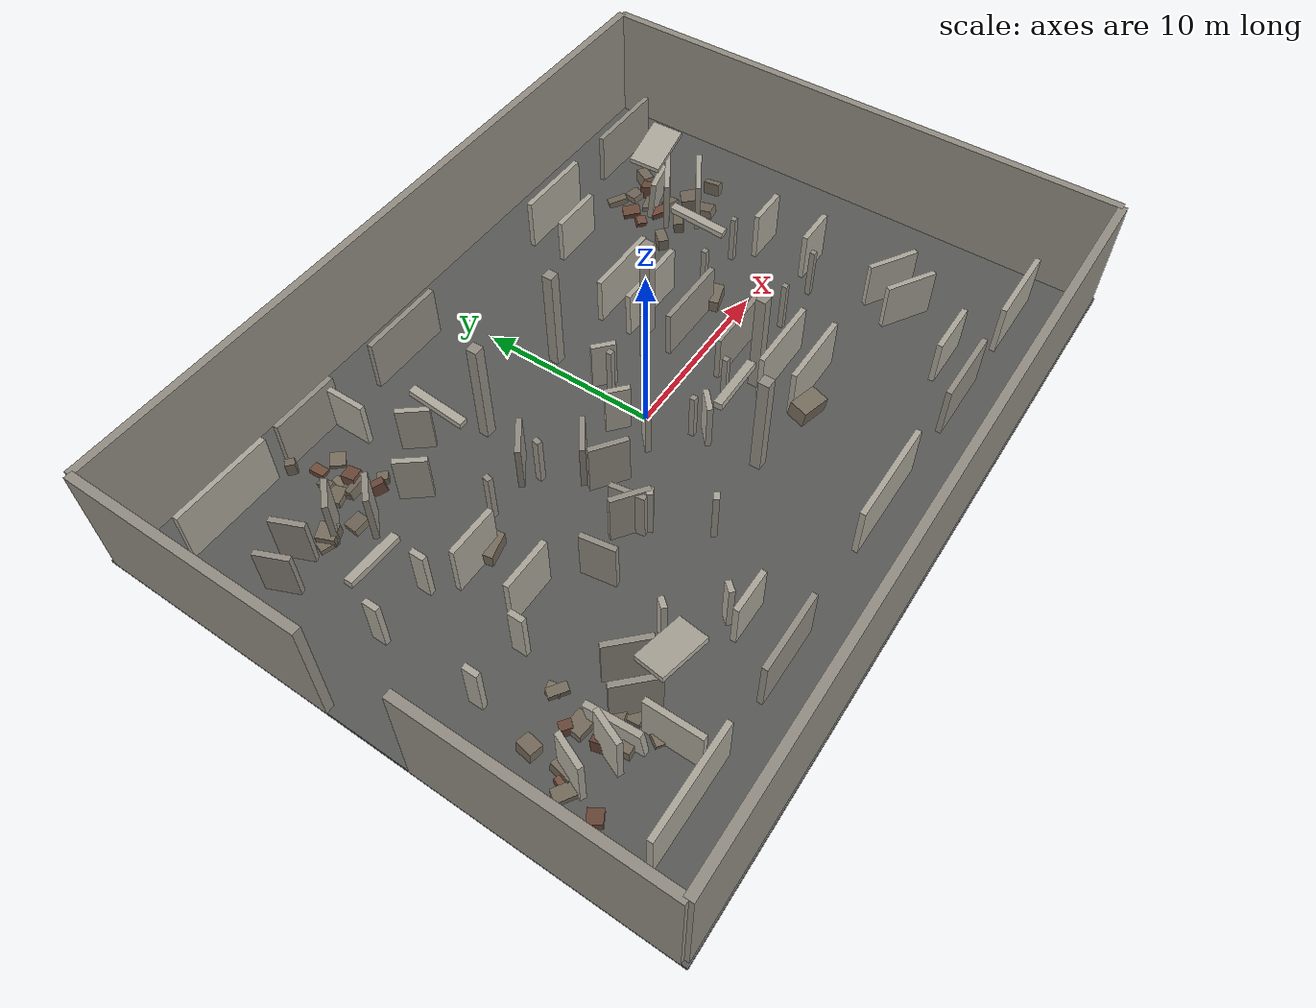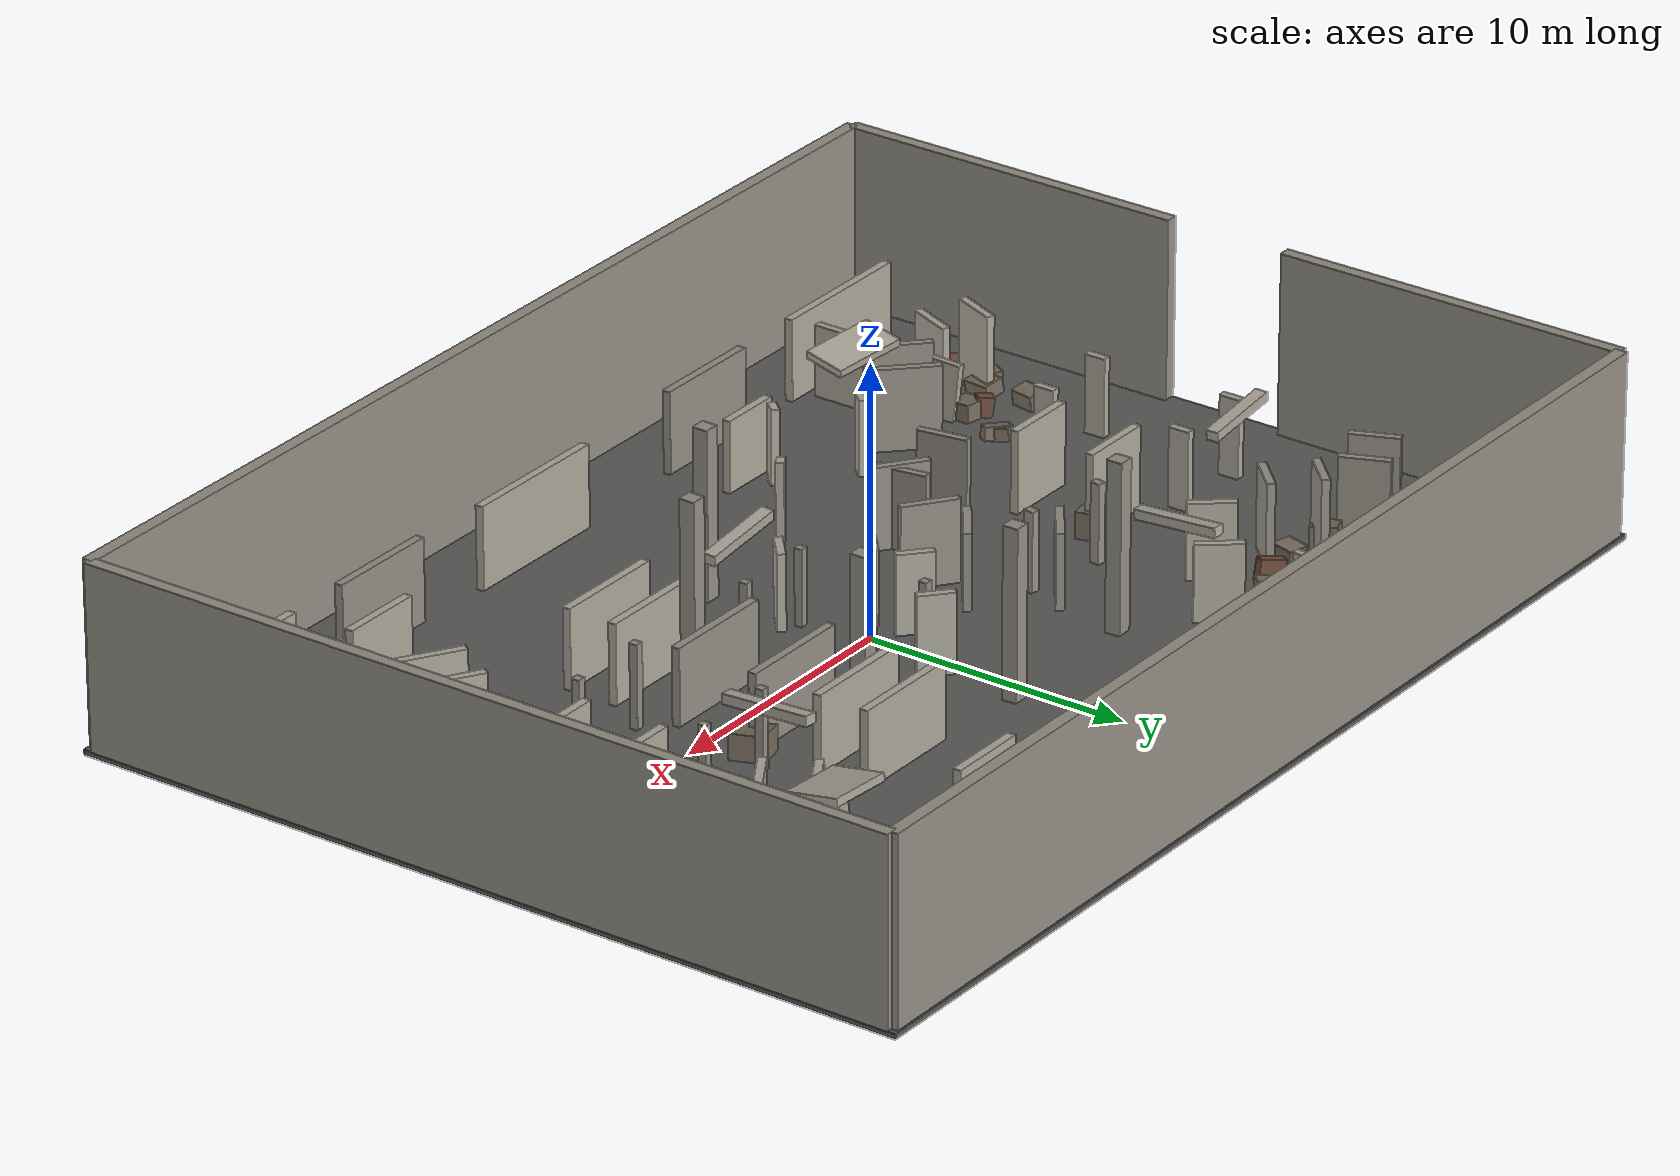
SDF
<?xml version="1.0" ?>
<sdf version="1.6">
  <model name="ruins_urban_01_challenge">
    <static>true</static>
    <link name="000_main_floor_slab">
      <pose>0.00000 0.00000 -0.10000 0.00000 0.00000 0.00000</pose>
      <visual name="visual">
        <geometry>
          <box><size>42.00000 32.00000 0.20000</size></box>
        </geometry>
          <material>
            <ambient>0.350 0.350 0.340 1</ambient>
            <diffuse>0.350 0.350 0.340 1</diffuse>
            <specular>0.03 0.03 0.03 1</specular>
          </material>
      </visual>
      <collision name="collision">
        <geometry>
          <box><size>42.00000 32.00000 0.20000</size></box>
        </geometry>
        <surface>
          <contact><collide_bitmask>0x01</collide_bitmask></contact>
          <friction>
            <ode><mu>1.0</mu><mu2>1.0</mu2></ode>
          </friction>
        </surface>
      </collision>
    </link>
    <link name="001_main_envelope_north">
      <pose>0.00000 15.70000 3.40000 0.00000 0.00000 0.00000</pose>
      <visual name="visual">
        <geometry>
          <box><size>41.60000 0.46000 6.80000</size></box>
        </geometry>
          <material>
            <ambient>0.580 0.560 0.520 1</ambient>
            <diffuse>0.580 0.560 0.520 1</diffuse>
            <specular>0.03 0.03 0.03 1</specular>
          </material>
      </visual>
      <collision name="collision">
        <geometry>
          <box><size>41.60000 0.46000 6.80000</size></box>
        </geometry>
        <surface>
          <contact><collide_bitmask>0x01</collide_bitmask></contact>
          <friction>
            <ode><mu>1.0</mu><mu2>1.0</mu2></ode>
          </friction>
        </surface>
      </collision>
    </link>
    <link name="002_main_envelope_south">
      <pose>0.00000 -15.70000 3.40000 0.00000 0.00000 0.00000</pose>
      <visual name="visual">
        <geometry>
          <box><size>41.60000 0.46000 6.80000</size></box>
        </geometry>
          <material>
            <ambient>0.580 0.560 0.520 1</ambient>
            <diffuse>0.580 0.560 0.520 1</diffuse>
            <specular>0.03 0.03 0.03 1</specular>
          </material>
      </visual>
      <collision name="collision">
        <geometry>
          <box><size>41.60000 0.46000 6.80000</size></box>
        </geometry>
        <surface>
          <contact><collide_bitmask>0x01</collide_bitmask></contact>
          <friction>
            <ode><mu>1.0</mu><mu2>1.0</mu2></ode>
          </friction>
        </surface>
      </collision>
    </link>
    <link name="003_main_envelope_west_n">
      <pose>-20.80000 9.00000 3.40000 0.00000 0.00000 -1.57080</pose>
      <visual name="visual">
        <geometry>
          <box><size>13.40000 0.46000 6.80000</size></box>
        </geometry>
          <material>
            <ambient>0.580 0.560 0.520 1</ambient>
            <diffuse>0.580 0.560 0.520 1</diffuse>
            <specular>0.03 0.03 0.03 1</specular>
          </material>
      </visual>
      <collision name="collision">
        <geometry>
          <box><size>13.40000 0.46000 6.80000</size></box>
        </geometry>
        <surface>
          <contact><collide_bitmask>0x01</collide_bitmask></contact>
          <friction>
            <ode><mu>1.0</mu><mu2>1.0</mu2></ode>
          </friction>
        </surface>
      </collision>
    </link>
    <link name="004_main_envelope_west_s">
      <pose>-20.80000 -9.00000 3.40000 0.00000 0.00000 -1.57080</pose>
      <visual name="visual">
        <geometry>
          <box><size>13.40000 0.46000 6.80000</size></box>
        </geometry>
          <material>
            <ambient>0.580 0.560 0.520 1</ambient>
            <diffuse>0.580 0.560 0.520 1</diffuse>
            <specular>0.03 0.03 0.03 1</specular>
          </material>
      </visual>
      <collision name="collision">
        <geometry>
          <box><size>13.40000 0.46000 6.80000</size></box>
        </geometry>
        <surface>
          <contact><collide_bitmask>0x01</collide_bitmask></contact>
          <friction>
            <ode><mu>1.0</mu><mu2>1.0</mu2></ode>
          </friction>
        </surface>
      </collision>
    </link>
    <link name="005_main_envelope_east">
      <pose>20.80000 0.00000 3.40000 0.00000 0.00000 1.57080</pose>
      <visual name="visual">
        <geometry>
          <box><size>31.40000 0.46000 6.80000</size></box>
        </geometry>
          <material>
            <ambient>0.580 0.560 0.520 1</ambient>
            <diffuse>0.580 0.560 0.520 1</diffuse>
            <specular>0.03 0.03 0.03 1</specular>
          </material>
      </visual>
      <collision name="collision">
        <geometry>
          <box><size>31.40000 0.46000 6.80000</size></box>
        </geometry>
        <surface>
          <contact><collide_bitmask>0x01</collide_bitmask></contact>
          <friction>
            <ode><mu>1.0</mu><mu2>1.0</mu2></ode>
          </friction>
        </surface>
      </collision>
    </link>
    <link name="006_main_corridor_west_lobby_west_n1_left">
      <pose>-17.02500 2.75000 1.48500 0.00000 0.00000 1.57080</pose>
      <visual name="visual">
        <geometry>
          <box><size>0.80000 0.30000 2.97000</size></box>
        </geometry>
          <material>
            <ambient>0.680 0.660 0.610 1</ambient>
            <diffuse>0.680 0.660 0.610 1</diffuse>
            <specular>0.03 0.03 0.03 1</specular>
          </material>
      </visual>
      <collision name="collision">
        <geometry>
          <box><size>0.80000 0.30000 2.97000</size></box>
        </geometry>
        <surface>
          <contact><collide_bitmask>0x01</collide_bitmask></contact>
          <friction>
            <ode><mu>1.0</mu><mu2>1.0</mu2></ode>
          </friction>
        </surface>
      </collision>
    </link>
    <link name="007_main_corridor_west_lobby_west_n1_right">
      <pose>-13.97500 2.75000 1.48500 0.00000 0.00000 1.57080</pose>
      <visual name="visual">
        <geometry>
          <box><size>0.80000 0.30000 2.97000</size></box>
        </geometry>
          <material>
            <ambient>0.680 0.660 0.610 1</ambient>
            <diffuse>0.680 0.660 0.610 1</diffuse>
            <specular>0.03 0.03 0.03 1</specular>
          </material>
      </visual>
      <collision name="collision">
        <geometry>
          <box><size>0.80000 0.30000 2.97000</size></box>
        </geometry>
        <surface>
          <contact><collide_bitmask>0x01</collide_bitmask></contact>
          <friction>
            <ode><mu>1.0</mu><mu2>1.0</mu2></ode>
          </friction>
        </surface>
      </collision>
    </link>
    <link name="008_main_corridor_west_n1_west_n2_left">
      <pose>-13.90407 8.40407 1.54500 0.00000 0.00000 0.78540</pose>
      <visual name="visual">
        <geometry>
          <box><size>1.66396 0.30000 3.09000</size></box>
        </geometry>
          <material>
            <ambient>0.580 0.560 0.520 1</ambient>
            <diffuse>0.580 0.560 0.520 1</diffuse>
            <specular>0.03 0.03 0.03 1</specular>
          </material>
      </visual>
      <collision name="collision">
        <geometry>
          <box><size>1.66396 0.30000 3.09000</size></box>
        </geometry>
        <surface>
          <contact><collide_bitmask>0x01</collide_bitmask></contact>
          <friction>
            <ode><mu>1.0</mu><mu2>1.0</mu2></ode>
          </friction>
        </surface>
      </collision>
    </link>
    <link name="009_main_corridor_west_n1_west_n2_right">
      <pose>-12.59593 7.09593 1.54500 0.00000 0.00000 0.78540</pose>
      <visual name="visual">
        <geometry>
          <box><size>1.66396 0.30000 3.09000</size></box>
        </geometry>
          <material>
            <ambient>0.580 0.560 0.520 1</ambient>
            <diffuse>0.580 0.560 0.520 1</diffuse>
            <specular>0.03 0.03 0.03 1</specular>
          </material>
      </visual>
      <collision name="collision">
        <geometry>
          <box><size>1.66396 0.30000 3.09000</size></box>
        </geometry>
        <surface>
          <contact><collide_bitmask>0x01</collide_bitmask></contact>
          <friction>
            <ode><mu>1.0</mu><mu2>1.0</mu2></ode>
          </friction>
        </surface>
      </collision>
    </link>
    <link name="010_main_corridor_west_n2_core_n_left">
      <pose>-7.80918 8.45266 1.42500 0.00000 0.00000 -0.89606</pose>
      <visual name="visual">
        <geometry>
          <box><size>1.70312 0.30000 2.85000</size></box>
        </geometry>
          <material>
            <ambient>0.680 0.660 0.610 1</ambient>
            <diffuse>0.680 0.660 0.610 1</diffuse>
            <specular>0.03 0.03 0.03 1</specular>
          </material>
      </visual>
      <collision name="collision">
        <geometry>
          <box><size>1.70312 0.30000 2.85000</size></box>
        </geometry>
        <surface>
          <contact><collide_bitmask>0x01</collide_bitmask></contact>
          <friction>
            <ode><mu>1.0</mu><mu2>1.0</mu2></ode>
          </friction>
        </surface>
      </collision>
    </link>
    <link name="011_main_corridor_west_n2_core_n_right">
      <pose>-10.19082 6.54734 1.42500 0.00000 0.00000 -0.89606</pose>
      <visual name="visual">
        <geometry>
          <box><size>1.70312 0.30000 2.85000</size></box>
        </geometry>
          <material>
            <ambient>0.680 0.660 0.610 1</ambient>
            <diffuse>0.680 0.660 0.610 1</diffuse>
            <specular>0.03 0.03 0.03 1</specular>
          </material>
      </visual>
      <collision name="collision">
        <geometry>
          <box><size>1.70312 0.30000 2.85000</size></box>
        </geometry>
        <surface>
          <contact><collide_bitmask>0x01</collide_bitmask></contact>
          <friction>
            <ode><mu>1.0</mu><mu2>1.0</mu2></ode>
          </friction>
        </surface>
      </collision>
    </link>
    <link name="012_main_corridor_core_n_core_w_left">
      <pose>-6.00461 2.20092 1.48500 0.00000 0.00000 -1.76819</pose>
      <visual name="visual">
        <geometry>
          <box><size>0.39902 0.30000 2.97000</size></box>
        </geometry>
          <material>
            <ambient>0.580 0.560 0.520 1</ambient>
            <diffuse>0.580 0.560 0.520 1</diffuse>
            <specular>0.03 0.03 0.03 1</specular>
          </material>
      </visual>
      <collision name="collision">
        <geometry>
          <box><size>0.39902 0.30000 2.97000</size></box>
        </geometry>
        <surface>
          <contact><collide_bitmask>0x01</collide_bitmask></contact>
          <friction>
            <ode><mu>1.0</mu><mu2>1.0</mu2></ode>
          </friction>
        </surface>
      </collision>
    </link>
    <link name="013_main_corridor_core_n_core_w_right">
      <pose>-8.99539 2.79908 1.48500 0.00000 0.00000 -1.76819</pose>
      <visual name="visual">
        <geometry>
          <box><size>0.39902 0.30000 2.97000</size></box>
        </geometry>
          <material>
            <ambient>0.580 0.560 0.520 1</ambient>
            <diffuse>0.580 0.560 0.520 1</diffuse>
            <specular>0.03 0.03 0.03 1</specular>
          </material>
      </visual>
      <collision name="collision">
        <geometry>
          <box><size>0.39902 0.30000 2.97000</size></box>
        </geometry>
        <surface>
          <contact><collide_bitmask>0x01</collide_bitmask></contact>
          <friction>
            <ode><mu>1.0</mu><mu2>1.0</mu2></ode>
          </friction>
        </surface>
      </collision>
    </link>
    <link name="014_main_corridor_core_w_west_lobby_left">
      <pose>-11.75000 -1.52500 1.54500 0.00000 0.00000 3.14159</pose>
      <visual name="visual">
        <geometry>
          <box><size>2.80000 0.30000 3.09000</size></box>
        </geometry>
          <material>
            <ambient>0.680 0.660 0.610 1</ambient>
            <diffuse>0.680 0.660 0.610 1</diffuse>
            <specular>0.03 0.03 0.03 1</specular>
          </material>
      </visual>
      <collision name="collision">
        <geometry>
          <box><size>2.80000 0.30000 3.09000</size></box>
        </geometry>
        <surface>
          <contact><collide_bitmask>0x01</collide_bitmask></contact>
          <friction>
            <ode><mu>1.0</mu><mu2>1.0</mu2></ode>
          </friction>
        </surface>
      </collision>
    </link>
    <link name="015_main_corridor_core_w_west_lobby_right">
      <pose>-11.75000 1.52500 1.54500 0.00000 0.00000 3.14159</pose>
      <visual name="visual">
        <geometry>
          <box><size>2.80000 0.30000 3.09000</size></box>
        </geometry>
          <material>
            <ambient>0.680 0.660 0.610 1</ambient>
            <diffuse>0.680 0.660 0.610 1</diffuse>
            <specular>0.03 0.03 0.03 1</specular>
          </material>
      </visual>
      <collision name="collision">
        <geometry>
          <box><size>2.80000 0.30000 3.09000</size></box>
        </geometry>
        <surface>
          <contact><collide_bitmask>0x01</collide_bitmask></contact>
          <friction>
            <ode><mu>1.0</mu><mu2>1.0</mu2></ode>
          </friction>
        </surface>
      </collision>
    </link>
    <link name="016_main_corridor_west_n1_west_n_dead_left">
      <pose>-17.58077 8.15385 1.42500 0.00000 0.00000 1.96559</pose>
      <visual name="visual">
        <geometry>
          <box><size>1.80000 0.30000 2.85000</size></box>
        </geometry>
          <material>
            <ambient>0.580 0.560 0.520 1</ambient>
            <diffuse>0.580 0.560 0.520 1</diffuse>
            <specular>0.03 0.03 0.03 1</specular>
          </material>
      </visual>
      <collision name="collision">
        <geometry>
          <box><size>1.80000 0.30000 2.85000</size></box>
        </geometry>
        <surface>
          <contact><collide_bitmask>0x01</collide_bitmask></contact>
          <friction>
            <ode><mu>1.0</mu><mu2>1.0</mu2></ode>
          </friction>
        </surface>
      </collision>
    </link>
    <link name="017_main_corridor_west_n1_west_n_dead_right">
      <pose>-15.91923 8.84615 1.42500 0.00000 0.00000 1.96559</pose>
      <visual name="visual">
        <geometry>
          <box><size>1.80000 0.30000 2.85000</size></box>
        </geometry>
          <material>
            <ambient>0.580 0.560 0.520 1</ambient>
            <diffuse>0.580 0.560 0.520 1</diffuse>
            <specular>0.03 0.03 0.03 1</specular>
          </material>
      </visual>
      <collision name="collision">
        <geometry>
          <box><size>1.80000 0.30000 2.85000</size></box>
        </geometry>
        <surface>
          <contact><collide_bitmask>0x01</collide_bitmask></contact>
          <friction>
            <ode><mu>1.0</mu><mu2>1.0</mu2></ode>
          </friction>
        </surface>
      </collision>
    </link>
    <link name="018_main_corridor_west_lobby_west_s1_left">
      <pose>-13.97500 -2.75000 1.48500 0.00000 0.00000 -1.57080</pose>
      <visual name="visual">
        <geometry>
          <box><size>0.80000 0.30000 2.97000</size></box>
        </geometry>
          <material>
            <ambient>0.680 0.660 0.610 1</ambient>
            <diffuse>0.680 0.660 0.610 1</diffuse>
            <specular>0.03 0.03 0.03 1</specular>
          </material>
      </visual>
      <collision name="collision">
        <geometry>
          <box><size>0.80000 0.30000 2.97000</size></box>
        </geometry>
        <surface>
          <contact><collide_bitmask>0x01</collide_bitmask></contact>
          <friction>
            <ode><mu>1.0</mu><mu2>1.0</mu2></ode>
          </friction>
        </surface>
      </collision>
    </link>
    <link name="019_main_corridor_west_lobby_west_s1_right">
      <pose>-17.02500 -2.75000 1.48500 0.00000 0.00000 -1.57080</pose>
      <visual name="visual">
        <geometry>
          <box><size>0.80000 0.30000 2.97000</size></box>
        </geometry>
          <material>
            <ambient>0.680 0.660 0.610 1</ambient>
            <diffuse>0.680 0.660 0.610 1</diffuse>
            <specular>0.03 0.03 0.03 1</specular>
          </material>
      </visual>
      <collision name="collision">
        <geometry>
          <box><size>0.80000 0.30000 2.97000</size></box>
        </geometry>
        <surface>
          <contact><collide_bitmask>0x01</collide_bitmask></contact>
          <friction>
            <ode><mu>1.0</mu><mu2>1.0</mu2></ode>
          </friction>
        </surface>
      </collision>
    </link>
    <link name="020_main_corridor_west_s1_west_s2_left">
      <pose>-12.34593 -7.34593 1.54500 0.00000 0.00000 -0.78540</pose>
      <visual name="visual">
        <geometry>
          <box><size>2.37107 0.30000 3.09000</size></box>
        </geometry>
          <material>
            <ambient>0.580 0.560 0.520 1</ambient>
            <diffuse>0.580 0.560 0.520 1</diffuse>
            <specular>0.03 0.03 0.03 1</specular>
          </material>
      </visual>
      <collision name="collision">
        <geometry>
          <box><size>2.37107 0.30000 3.09000</size></box>
        </geometry>
        <surface>
          <contact><collide_bitmask>0x01</collide_bitmask></contact>
          <friction>
            <ode><mu>1.0</mu><mu2>1.0</mu2></ode>
          </friction>
        </surface>
      </collision>
    </link>
    <link name="021_main_corridor_west_s1_west_s2_right">
      <pose>-13.65407 -8.65407 1.54500 0.00000 0.00000 -0.78540</pose>
      <visual name="visual">
        <geometry>
          <box><size>2.37107 0.30000 3.09000</size></box>
        </geometry>
          <material>
            <ambient>0.580 0.560 0.520 1</ambient>
            <diffuse>0.580 0.560 0.520 1</diffuse>
            <specular>0.03 0.03 0.03 1</specular>
          </material>
      </visual>
      <collision name="collision">
        <geometry>
          <box><size>2.37107 0.30000 3.09000</size></box>
        </geometry>
        <surface>
          <contact><collide_bitmask>0x01</collide_bitmask></contact>
          <friction>
            <ode><mu>1.0</mu><mu2>1.0</mu2></ode>
          </friction>
        </surface>
      </collision>
    </link>
    <link name="022_main_corridor_west_s2_core_s_left">
      <pose>-9.89768 -7.49578 1.42500 0.00000 0.00000 0.85197</pose>
      <visual name="visual">
        <geometry>
          <box><size>0.61507 0.30000 2.85000</size></box>
        </geometry>
          <material>
            <ambient>0.680 0.660 0.610 1</ambient>
            <diffuse>0.680 0.660 0.610 1</diffuse>
            <specular>0.03 0.03 0.03 1</specular>
          </material>
      </visual>
      <collision name="collision">
        <geometry>
          <box><size>0.61507 0.30000 2.85000</size></box>
        </geometry>
        <surface>
          <contact><collide_bitmask>0x01</collide_bitmask></contact>
          <friction>
            <ode><mu>1.0</mu><mu2>1.0</mu2></ode>
          </friction>
        </surface>
      </collision>
    </link>
    <link name="023_main_corridor_west_s2_core_s_right">
      <pose>-7.60232 -9.50422 1.42500 0.00000 0.00000 0.85197</pose>
      <visual name="visual">
        <geometry>
          <box><size>0.61507 0.30000 2.85000</size></box>
        </geometry>
          <material>
            <ambient>0.680 0.660 0.610 1</ambient>
            <diffuse>0.680 0.660 0.610 1</diffuse>
            <specular>0.03 0.03 0.03 1</specular>
          </material>
      </visual>
      <collision name="collision">
        <geometry>
          <box><size>0.61507 0.30000 2.85000</size></box>
        </geometry>
        <surface>
          <contact><collide_bitmask>0x01</collide_bitmask></contact>
          <friction>
            <ode><mu>1.0</mu><mu2>1.0</mu2></ode>
          </friction>
        </surface>
      </collision>
    </link>
    <link name="024_main_corridor_core_s_core_w_left">
      <pose>-9.00727 -3.48189 1.48500 0.00000 0.00000 1.72345</pose>
      <visual name="visual">
        <geometry>
          <box><size>1.87647 0.30000 2.97000</size></box>
        </geometry>
          <material>
            <ambient>0.580 0.560 0.520 1</ambient>
            <diffuse>0.580 0.560 0.520 1</diffuse>
            <specular>0.03 0.03 0.03 1</specular>
          </material>
      </visual>
      <collision name="collision">
        <geometry>
          <box><size>1.87647 0.30000 2.97000</size></box>
        </geometry>
        <surface>
          <contact><collide_bitmask>0x01</collide_bitmask></contact>
          <friction>
            <ode><mu>1.0</mu><mu2>1.0</mu2></ode>
          </friction>
        </surface>
      </collision>
    </link>
    <link name="025_main_corridor_core_s_core_w_right">
      <pose>-5.99273 -3.01811 1.48500 0.00000 0.00000 1.72345</pose>
      <visual name="visual">
        <geometry>
          <box><size>1.87647 0.30000 2.97000</size></box>
        </geometry>
          <material>
            <ambient>0.580 0.560 0.520 1</ambient>
            <diffuse>0.580 0.560 0.520 1</diffuse>
            <specular>0.03 0.03 0.03 1</specular>
          </material>
      </visual>
      <collision name="collision">
        <geometry>
          <box><size>1.87647 0.30000 2.97000</size></box>
        </geometry>
        <surface>
          <contact><collide_bitmask>0x01</collide_bitmask></contact>
          <friction>
            <ode><mu>1.0</mu><mu2>1.0</mu2></ode>
          </friction>
        </surface>
      </collision>
    </link>
    <link name="026_main_corridor_west_s1_west_s_dead_left">
      <pose>-15.91923 -8.84615 1.54500 0.00000 0.00000 -1.96559</pose>
      <visual name="visual">
        <geometry>
          <box><size>1.80000 0.30000 3.09000</size></box>
        </geometry>
          <material>
            <ambient>0.680 0.660 0.610 1</ambient>
            <diffuse>0.680 0.660 0.610 1</diffuse>
            <specular>0.03 0.03 0.03 1</specular>
          </material>
      </visual>
      <collision name="collision">
        <geometry>
          <box><size>1.80000 0.30000 3.09000</size></box>
        </geometry>
        <surface>
          <contact><collide_bitmask>0x01</collide_bitmask></contact>
          <friction>
            <ode><mu>1.0</mu><mu2>1.0</mu2></ode>
          </friction>
        </surface>
      </collision>
    </link>
    <link name="027_main_corridor_west_s1_west_s_dead_right">
      <pose>-17.58077 -8.15385 1.54500 0.00000 0.00000 -1.96559</pose>
      <visual name="visual">
        <geometry>
          <box><size>1.80000 0.30000 3.09000</size></box>
        </geometry>
          <material>
            <ambient>0.680 0.660 0.610 1</ambient>
            <diffuse>0.680 0.660 0.610 1</diffuse>
            <specular>0.03 0.03 0.03 1</specular>
          </material>
      </visual>
      <collision name="collision">
        <geometry>
          <box><size>1.80000 0.30000 3.09000</size></box>
        </geometry>
        <surface>
          <contact><collide_bitmask>0x01</collide_bitmask></contact>
          <friction>
            <ode><mu>1.0</mu><mu2>1.0</mu2></ode>
          </friction>
        </surface>
      </collision>
    </link>
    <link name="028_main_corridor_core_w_atrium_n_left">
      <pose>-6.14696 3.23332 1.42500 0.00000 0.00000 0.62880</pose>
      <visual name="visual">
        <geometry>
          <box><size>2.10074 0.30000 2.85000</size></box>
        </geometry>
          <material>
            <ambient>0.580 0.560 0.520 1</ambient>
            <diffuse>0.580 0.560 0.520 1</diffuse>
            <specular>0.03 0.03 0.03 1</specular>
          </material>
      </visual>
      <collision name="collision">
        <geometry>
          <box><size>2.10074 0.30000 2.85000</size></box>
        </geometry>
        <surface>
          <contact><collide_bitmask>0x01</collide_bitmask></contact>
          <friction>
            <ode><mu>1.0</mu><mu2>1.0</mu2></ode>
          </friction>
        </surface>
      </collision>
    </link>
    <link name="029_main_corridor_core_w_atrium_n_right">
      <pose>-4.35304 0.76668 1.42500 0.00000 0.00000 0.62880</pose>
      <visual name="visual">
        <geometry>
          <box><size>2.10074 0.30000 2.85000</size></box>
        </geometry>
          <material>
            <ambient>0.580 0.560 0.520 1</ambient>
            <diffuse>0.580 0.560 0.520 1</diffuse>
            <specular>0.03 0.03 0.03 1</specular>
          </material>
      </visual>
      <collision name="collision">
        <geometry>
          <box><size>2.10074 0.30000 2.85000</size></box>
        </geometry>
        <surface>
          <contact><collide_bitmask>0x01</collide_bitmask></contact>
          <friction>
            <ode><mu>1.0</mu><mu2>1.0</mu2></ode>
          </friction>
        </surface>
      </collision>
    </link>
    <link name="030_main_corridor_atrium_n_central_left">
      <pose>0.76315 3.13980 1.48500 0.00000 0.00000 -0.72664</pose>
      <visual name="visual">
        <geometry>
          <box><size>1.32080 0.30000 2.97000</size></box>
        </geometry>
          <material>
            <ambient>0.680 0.660 0.610 1</ambient>
            <diffuse>0.680 0.660 0.610 1</diffuse>
            <specular>0.03 0.03 0.03 1</specular>
          </material>
      </visual>
      <collision name="collision">
        <geometry>
          <box><size>1.32080 0.30000 2.97000</size></box>
        </geometry>
        <surface>
          <contact><collide_bitmask>0x01</collide_bitmask></contact>
          <friction>
            <ode><mu>1.0</mu><mu2>1.0</mu2></ode>
          </friction>
        </surface>
      </collision>
    </link>
    <link name="031_main_corridor_atrium_n_central_right">
      <pose>-1.26315 0.86020 1.48500 0.00000 0.00000 -0.72664</pose>
      <visual name="visual">
        <geometry>
          <box><size>1.32080 0.30000 2.97000</size></box>
        </geometry>
          <material>
            <ambient>0.680 0.660 0.610 1</ambient>
            <diffuse>0.680 0.660 0.610 1</diffuse>
            <specular>0.03 0.03 0.03 1</specular>
          </material>
      </visual>
      <collision name="collision">
        <geometry>
          <box><size>1.32080 0.30000 2.97000</size></box>
        </geometry>
        <surface>
          <contact><collide_bitmask>0x01</collide_bitmask></contact>
          <friction>
            <ode><mu>1.0</mu><mu2>1.0</mu2></ode>
          </friction>
        </surface>
      </collision>
    </link>
    <link name="032_main_corridor_core_w_atrium_s_left">
      <pose>-4.35304 -0.76668 1.54500 0.00000 0.00000 -0.62880</pose>
      <visual name="visual">
        <geometry>
          <box><size>2.10074 0.30000 3.09000</size></box>
        </geometry>
          <material>
            <ambient>0.580 0.560 0.520 1</ambient>
            <diffuse>0.580 0.560 0.520 1</diffuse>
            <specular>0.03 0.03 0.03 1</specular>
          </material>
      </visual>
      <collision name="collision">
        <geometry>
          <box><size>2.10074 0.30000 3.09000</size></box>
        </geometry>
        <surface>
          <contact><collide_bitmask>0x01</collide_bitmask></contact>
          <friction>
            <ode><mu>1.0</mu><mu2>1.0</mu2></ode>
          </friction>
        </surface>
      </collision>
    </link>
    <link name="033_main_corridor_core_w_atrium_s_right">
      <pose>-6.14696 -3.23332 1.54500 0.00000 0.00000 -0.62880</pose>
      <visual name="visual">
        <geometry>
          <box><size>2.10074 0.30000 3.09000</size></box>
        </geometry>
          <material>
            <ambient>0.580 0.560 0.520 1</ambient>
            <diffuse>0.580 0.560 0.520 1</diffuse>
            <specular>0.03 0.03 0.03 1</specular>
          </material>
      </visual>
      <collision name="collision">
        <geometry>
          <box><size>2.10074 0.30000 3.09000</size></box>
        </geometry>
        <surface>
          <contact><collide_bitmask>0x01</collide_bitmask></contact>
          <friction>
            <ode><mu>1.0</mu><mu2>1.0</mu2></ode>
          </friction>
        </surface>
      </collision>
    </link>
    <link name="034_main_corridor_atrium_s_central_left">
      <pose>-1.26315 -0.86020 1.42500 0.00000 0.00000 0.72664</pose>
      <visual name="visual">
        <geometry>
          <box><size>1.32080 0.30000 2.85000</size></box>
        </geometry>
          <material>
            <ambient>0.680 0.660 0.610 1</ambient>
            <diffuse>0.680 0.660 0.610 1</diffuse>
            <specular>0.03 0.03 0.03 1</specular>
          </material>
      </visual>
      <collision name="collision">
        <geometry>
          <box><size>1.32080 0.30000 2.85000</size></box>
        </geometry>
        <surface>
          <contact><collide_bitmask>0x01</collide_bitmask></contact>
          <friction>
            <ode><mu>1.0</mu><mu2>1.0</mu2></ode>
          </friction>
        </surface>
      </collision>
    </link>
    <link name="035_main_corridor_atrium_s_central_right">
      <pose>0.76315 -3.13980 1.42500 0.00000 0.00000 0.72664</pose>
      <visual name="visual">
        <geometry>
          <box><size>1.32080 0.30000 2.85000</size></box>
        </geometry>
          <material>
            <ambient>0.680 0.660 0.610 1</ambient>
            <diffuse>0.680 0.660 0.610 1</diffuse>
            <specular>0.03 0.03 0.03 1</specular>
          </material>
      </visual>
      <collision name="collision">
        <geometry>
          <box><size>1.32080 0.30000 2.85000</size></box>
        </geometry>
        <surface>
          <contact><collide_bitmask>0x01</collide_bitmask></contact>
          <friction>
            <ode><mu>1.0</mu><mu2>1.0</mu2></ode>
          </friction>
        </surface>
      </collision>
    </link>
    <link name="036_main_corridor_core_s_atrium_s_left">
      <pose>-5.49061 -3.91691 1.54500 0.00000 0.00000 0.50710</pose>
      <visual name="visual">
        <geometry>
          <box><size>0.44782 0.30000 3.09000</size></box>
        </geometry>
          <material>
            <ambient>0.680 0.660 0.610 1</ambient>
            <diffuse>0.680 0.660 0.610 1</diffuse>
            <specular>0.03 0.03 0.03 1</specular>
          </material>
      </visual>
      <collision name="collision">
        <geometry>
          <box><size>0.44782 0.30000 3.09000</size></box>
        </geometry>
        <surface>
          <contact><collide_bitmask>0x01</collide_bitmask></contact>
          <friction>
            <ode><mu>1.0</mu><mu2>1.0</mu2></ode>
          </friction>
        </surface>
      </collision>
    </link>
    <link name="037_main_corridor_core_s_atrium_s_right">
      <pose>-4.00939 -6.58309 1.54500 0.00000 0.00000 0.50710</pose>
      <visual name="visual">
        <geometry>
          <box><size>0.44782 0.30000 3.09000</size></box>
        </geometry>
          <material>
            <ambient>0.680 0.660 0.610 1</ambient>
            <diffuse>0.680 0.660 0.610 1</diffuse>
            <specular>0.03 0.03 0.03 1</specular>
          </material>
      </visual>
      <collision name="collision">
        <geometry>
          <box><size>0.44782 0.30000 3.09000</size></box>
        </geometry>
        <surface>
          <contact><collide_bitmask>0x01</collide_bitmask></contact>
          <friction>
            <ode><mu>1.0</mu><mu2>1.0</mu2></ode>
          </friction>
        </surface>
      </collision>
    </link>
    <link name="038_main_corridor_central_east_core_left">
      <pose>6.50000 1.52500 1.42500 0.00000 0.00000 0.00000</pose>
      <visual name="visual">
        <geometry>
          <box><size>4.30000 0.30000 2.85000</size></box>
        </geometry>
          <material>
            <ambient>0.580 0.560 0.520 1</ambient>
            <diffuse>0.580 0.560 0.520 1</diffuse>
            <specular>0.03 0.03 0.03 1</specular>
          </material>
      </visual>
      <collision name="collision">
        <geometry>
          <box><size>4.30000 0.30000 2.85000</size></box>
        </geometry>
        <surface>
          <contact><collide_bitmask>0x01</collide_bitmask></contact>
          <friction>
            <ode><mu>1.0</mu><mu2>1.0</mu2></ode>
          </friction>
        </surface>
      </collision>
    </link>
    <link name="039_main_corridor_central_east_core_right">
      <pose>6.50000 -1.52500 1.42500 0.00000 0.00000 0.00000</pose>
      <visual name="visual">
        <geometry>
          <box><size>4.30000 0.30000 2.85000</size></box>
        </geometry>
          <material>
            <ambient>0.580 0.560 0.520 1</ambient>
            <diffuse>0.580 0.560 0.520 1</diffuse>
            <specular>0.03 0.03 0.03 1</specular>
          </material>
      </visual>
      <collision name="collision">
        <geometry>
          <box><size>4.30000 0.30000 2.85000</size></box>
        </geometry>
        <surface>
          <contact><collide_bitmask>0x01</collide_bitmask></contact>
          <friction>
            <ode><mu>1.0</mu><mu2>1.0</mu2></ode>
          </friction>
        </surface>
      </collision>
    </link>
    <link name="040_main_corridor_east_core_east_exit_left">
      <pose>14.50000 1.52500 1.48500 0.00000 0.00000 0.00000</pose>
      <visual name="visual">
        <geometry>
          <box><size>2.30000 0.30000 2.97000</size></box>
        </geometry>
          <material>
            <ambient>0.680 0.660 0.610 1</ambient>
            <diffuse>0.680 0.660 0.610 1</diffuse>
            <specular>0.03 0.03 0.03 1</specular>
          </material>
      </visual>
      <collision name="collision">
        <geometry>
          <box><size>2.30000 0.30000 2.97000</size></box>
        </geometry>
        <surface>
          <contact><collide_bitmask>0x01</collide_bitmask></contact>
          <friction>
            <ode><mu>1.0</mu><mu2>1.0</mu2></ode>
          </friction>
        </surface>
      </collision>
    </link>
    <link name="041_main_corridor_east_core_east_exit_right">
      <pose>14.50000 -1.52500 1.48500 0.00000 0.00000 0.00000</pose>
      <visual name="visual">
        <geometry>
          <box><size>2.30000 0.30000 2.97000</size></box>
        </geometry>
          <material>
            <ambient>0.680 0.660 0.610 1</ambient>
            <diffuse>0.680 0.660 0.610 1</diffuse>
            <specular>0.03 0.03 0.03 1</specular>
          </material>
      </visual>
      <collision name="collision">
        <geometry>
          <box><size>2.30000 0.30000 2.97000</size></box>
        </geometry>
        <surface>
          <contact><collide_bitmask>0x01</collide_bitmask></contact>
          <friction>
            <ode><mu>1.0</mu><mu2>1.0</mu2></ode>
          </friction>
        </surface>
      </collision>
    </link>
    <link name="042_main_corridor_central_east_n1_left">
      <pose>0.47500 2.50000 1.54500 0.00000 0.00000 1.57080</pose>
      <visual name="visual">
        <geometry>
          <box><size>0.30000 0.30000 3.09000</size></box>
        </geometry>
          <material>
            <ambient>0.580 0.560 0.520 1</ambient>
            <diffuse>0.580 0.560 0.520 1</diffuse>
            <specular>0.03 0.03 0.03 1</specular>
          </material>
      </visual>
      <collision name="collision">
        <geometry>
          <box><size>0.30000 0.30000 3.09000</size></box>
        </geometry>
        <surface>
          <contact><collide_bitmask>0x01</collide_bitmask></contact>
          <friction>
            <ode><mu>1.0</mu><mu2>1.0</mu2></ode>
          </friction>
        </surface>
      </collision>
    </link>
    <link name="043_main_corridor_central_east_n1_right">
      <pose>3.52500 2.50000 1.54500 0.00000 0.00000 1.57080</pose>
      <visual name="visual">
        <geometry>
          <box><size>0.30000 0.30000 3.09000</size></box>
        </geometry>
          <material>
            <ambient>0.580 0.560 0.520 1</ambient>
            <diffuse>0.580 0.560 0.520 1</diffuse>
            <specular>0.03 0.03 0.03 1</specular>
          </material>
      </visual>
      <collision name="collision">
        <geometry>
          <box><size>0.30000 0.30000 3.09000</size></box>
        </geometry>
        <surface>
          <contact><collide_bitmask>0x01</collide_bitmask></contact>
          <friction>
            <ode><mu>1.0</mu><mu2>1.0</mu2></ode>
          </friction>
        </surface>
      </collision>
    </link>
    <link name="044_main_corridor_east_n1_east_n2_left">
      <pose>6.50000 5.92500 1.42500 0.00000 0.00000 0.00000</pose>
      <visual name="visual">
        <geometry>
          <box><size>4.30000 0.30000 2.85000</size></box>
        </geometry>
          <material>
            <ambient>0.680 0.660 0.610 1</ambient>
            <diffuse>0.680 0.660 0.610 1</diffuse>
            <specular>0.03 0.03 0.03 1</specular>
          </material>
      </visual>
      <collision name="collision">
        <geometry>
          <box><size>4.30000 0.30000 2.85000</size></box>
        </geometry>
        <surface>
          <contact><collide_bitmask>0x01</collide_bitmask></contact>
          <friction>
            <ode><mu>1.0</mu><mu2>1.0</mu2></ode>
          </friction>
        </surface>
      </collision>
    </link>
    <link name="045_main_corridor_east_n1_east_n2_right">
      <pose>6.50000 4.07500 1.42500 0.00000 0.00000 0.00000</pose>
      <visual name="visual">
        <geometry>
          <box><size>4.30000 0.30000 2.85000</size></box>
        </geometry>
          <material>
            <ambient>0.680 0.660 0.610 1</ambient>
            <diffuse>0.680 0.660 0.610 1</diffuse>
            <specular>0.03 0.03 0.03 1</specular>
          </material>
      </visual>
      <collision name="collision">
        <geometry>
          <box><size>4.30000 0.30000 2.85000</size></box>
        </geometry>
        <surface>
          <contact><collide_bitmask>0x01</collide_bitmask></contact>
          <friction>
            <ode><mu>1.0</mu><mu2>1.0</mu2></ode>
          </friction>
        </surface>
      </collision>
    </link>
    <link name="046_main_corridor_east_n2_east_core_left">
      <pose>12.52500 2.50000 1.48500 0.00000 0.00000 -1.57080</pose>
      <visual name="visual">
        <geometry>
          <box><size>0.30000 0.30000 2.97000</size></box>
        </geometry>
          <material>
            <ambient>0.580 0.560 0.520 1</ambient>
            <diffuse>0.580 0.560 0.520 1</diffuse>
            <specular>0.03 0.03 0.03 1</specular>
          </material>
      </visual>
      <collision name="collision">
        <geometry>
          <box><size>0.30000 0.30000 2.97000</size></box>
        </geometry>
        <surface>
          <contact><collide_bitmask>0x01</collide_bitmask></contact>
          <friction>
            <ode><mu>1.0</mu><mu2>1.0</mu2></ode>
          </friction>
        </surface>
      </collision>
    </link>
    <link name="047_main_corridor_east_n2_east_core_right">
      <pose>9.47500 2.50000 1.48500 0.00000 0.00000 -1.57080</pose>
      <visual name="visual">
        <geometry>
          <box><size>0.30000 0.30000 2.97000</size></box>
        </geometry>
          <material>
            <ambient>0.580 0.560 0.520 1</ambient>
            <diffuse>0.580 0.560 0.520 1</diffuse>
            <specular>0.03 0.03 0.03 1</specular>
          </material>
      </visual>
      <collision name="collision">
        <geometry>
          <box><size>0.30000 0.30000 2.97000</size></box>
        </geometry>
        <surface>
          <contact><collide_bitmask>0x01</collide_bitmask></contact>
          <friction>
            <ode><mu>1.0</mu><mu2>1.0</mu2></ode>
          </friction>
        </surface>
      </collision>
    </link>
    <link name="048_main_corridor_east_n2_east_n_dead_left">
      <pose>13.77831 7.76649 1.54500 0.00000 0.00000 0.55165</pose>
      <visual name="visual">
        <geometry>
          <box><size>2.93217 0.30000 3.09000</size></box>
        </geometry>
          <material>
            <ambient>0.680 0.660 0.610 1</ambient>
            <diffuse>0.680 0.660 0.610 1</diffuse>
            <specular>0.03 0.03 0.03 1</specular>
          </material>
      </visual>
      <collision name="collision">
        <geometry>
          <box><size>2.93217 0.30000 3.09000</size></box>
        </geometry>
        <surface>
          <contact><collide_bitmask>0x01</collide_bitmask></contact>
          <friction>
            <ode><mu>1.0</mu><mu2>1.0</mu2></ode>
          </friction>
        </surface>
      </collision>
    </link>
    <link name="049_main_corridor_east_n2_east_n_dead_right">
      <pose>14.72169 6.23351 1.54500 0.00000 0.00000 0.55165</pose>
      <visual name="visual">
        <geometry>
          <box><size>2.93217 0.30000 3.09000</size></box>
        </geometry>
          <material>
            <ambient>0.680 0.660 0.610 1</ambient>
            <diffuse>0.680 0.660 0.610 1</diffuse>
            <specular>0.03 0.03 0.03 1</specular>
          </material>
      </visual>
      <collision name="collision">
        <geometry>
          <box><size>2.93217 0.30000 3.09000</size></box>
        </geometry>
        <surface>
          <contact><collide_bitmask>0x01</collide_bitmask></contact>
          <friction>
            <ode><mu>1.0</mu><mu2>1.0</mu2></ode>
          </friction>
        </surface>
      </collision>
    </link>
    <link name="050_main_corridor_central_east_s1_left">
      <pose>3.52500 -2.50000 1.42500 0.00000 0.00000 -1.57080</pose>
      <visual name="visual">
        <geometry>
          <box><size>0.30000 0.30000 2.85000</size></box>
        </geometry>
          <material>
            <ambient>0.580 0.560 0.520 1</ambient>
            <diffuse>0.580 0.560 0.520 1</diffuse>
            <specular>0.03 0.03 0.03 1</specular>
          </material>
      </visual>
      <collision name="collision">
        <geometry>
          <box><size>0.30000 0.30000 2.85000</size></box>
        </geometry>
        <surface>
          <contact><collide_bitmask>0x01</collide_bitmask></contact>
          <friction>
            <ode><mu>1.0</mu><mu2>1.0</mu2></ode>
          </friction>
        </surface>
      </collision>
    </link>
    <link name="051_main_corridor_central_east_s1_right">
      <pose>0.47500 -2.50000 1.42500 0.00000 0.00000 -1.57080</pose>
      <visual name="visual">
        <geometry>
          <box><size>0.30000 0.30000 2.85000</size></box>
        </geometry>
          <material>
            <ambient>0.580 0.560 0.520 1</ambient>
            <diffuse>0.580 0.560 0.520 1</diffuse>
            <specular>0.03 0.03 0.03 1</specular>
          </material>
      </visual>
      <collision name="collision">
        <geometry>
          <box><size>0.30000 0.30000 2.85000</size></box>
        </geometry>
        <surface>
          <contact><collide_bitmask>0x01</collide_bitmask></contact>
          <friction>
            <ode><mu>1.0</mu><mu2>1.0</mu2></ode>
          </friction>
        </surface>
      </collision>
    </link>
    <link name="052_main_corridor_east_s1_east_s2_left">
      <pose>6.50000 -4.07500 1.48500 0.00000 0.00000 0.00000</pose>
      <visual name="visual">
        <geometry>
          <box><size>4.30000 0.30000 2.97000</size></box>
        </geometry>
          <material>
            <ambient>0.680 0.660 0.610 1</ambient>
            <diffuse>0.680 0.660 0.610 1</diffuse>
            <specular>0.03 0.03 0.03 1</specular>
          </material>
      </visual>
      <collision name="collision">
        <geometry>
          <box><size>4.30000 0.30000 2.97000</size></box>
        </geometry>
        <surface>
          <contact><collide_bitmask>0x01</collide_bitmask></contact>
          <friction>
            <ode><mu>1.0</mu><mu2>1.0</mu2></ode>
          </friction>
        </surface>
      </collision>
    </link>
    <link name="053_main_corridor_east_s1_east_s2_right">
      <pose>6.50000 -5.92500 1.48500 0.00000 0.00000 0.00000</pose>
      <visual name="visual">
        <geometry>
          <box><size>4.30000 0.30000 2.97000</size></box>
        </geometry>
          <material>
            <ambient>0.680 0.660 0.610 1</ambient>
            <diffuse>0.680 0.660 0.610 1</diffuse>
            <specular>0.03 0.03 0.03 1</specular>
          </material>
      </visual>
      <collision name="collision">
        <geometry>
          <box><size>4.30000 0.30000 2.97000</size></box>
        </geometry>
        <surface>
          <contact><collide_bitmask>0x01</collide_bitmask></contact>
          <friction>
            <ode><mu>1.0</mu><mu2>1.0</mu2></ode>
          </friction>
        </surface>
      </collision>
    </link>
    <link name="054_main_corridor_east_s2_east_core_left">
      <pose>9.47500 -2.50000 1.54500 0.00000 0.00000 1.57080</pose>
      <visual name="visual">
        <geometry>
          <box><size>0.30000 0.30000 3.09000</size></box>
        </geometry>
          <material>
            <ambient>0.580 0.560 0.520 1</ambient>
            <diffuse>0.580 0.560 0.520 1</diffuse>
            <specular>0.03 0.03 0.03 1</specular>
          </material>
      </visual>
      <collision name="collision">
        <geometry>
          <box><size>0.30000 0.30000 3.09000</size></box>
        </geometry>
        <surface>
          <contact><collide_bitmask>0x01</collide_bitmask></contact>
          <friction>
            <ode><mu>1.0</mu><mu2>1.0</mu2></ode>
          </friction>
        </surface>
      </collision>
    </link>
    <link name="055_main_corridor_east_s2_east_core_right">
      <pose>12.52500 -2.50000 1.54500 0.00000 0.00000 1.57080</pose>
      <visual name="visual">
        <geometry>
          <box><size>0.30000 0.30000 3.09000</size></box>
        </geometry>
          <material>
            <ambient>0.580 0.560 0.520 1</ambient>
            <diffuse>0.580 0.560 0.520 1</diffuse>
            <specular>0.03 0.03 0.03 1</specular>
          </material>
      </visual>
      <collision name="collision">
        <geometry>
          <box><size>0.30000 0.30000 3.09000</size></box>
        </geometry>
        <surface>
          <contact><collide_bitmask>0x01</collide_bitmask></contact>
          <friction>
            <ode><mu>1.0</mu><mu2>1.0</mu2></ode>
          </friction>
        </surface>
      </collision>
    </link>
    <link name="056_main_corridor_east_s2_east_s_dead_left">
      <pose>14.72169 -6.23351 1.42500 0.00000 0.00000 -0.55165</pose>
      <visual name="visual">
        <geometry>
          <box><size>2.93217 0.30000 2.85000</size></box>
        </geometry>
          <material>
            <ambient>0.680 0.660 0.610 1</ambient>
            <diffuse>0.680 0.660 0.610 1</diffuse>
            <specular>0.03 0.03 0.03 1</specular>
          </material>
      </visual>
      <collision name="collision">
        <geometry>
          <box><size>2.93217 0.30000 2.85000</size></box>
        </geometry>
        <surface>
          <contact><collide_bitmask>0x01</collide_bitmask></contact>
          <friction>
            <ode><mu>1.0</mu><mu2>1.0</mu2></ode>
          </friction>
        </surface>
      </collision>
    </link>
    <link name="057_main_corridor_east_s2_east_s_dead_right">
      <pose>13.77831 -7.76649 1.42500 0.00000 0.00000 -0.55165</pose>
      <visual name="visual">
        <geometry>
          <box><size>2.93217 0.30000 2.85000</size></box>
        </geometry>
          <material>
            <ambient>0.680 0.660 0.610 1</ambient>
            <diffuse>0.680 0.660 0.610 1</diffuse>
            <specular>0.03 0.03 0.03 1</specular>
          </material>
      </visual>
      <collision name="collision">
        <geometry>
          <box><size>2.93217 0.30000 2.85000</size></box>
        </geometry>
        <surface>
          <contact><collide_bitmask>0x01</collide_bitmask></contact>
          <friction>
            <ode><mu>1.0</mu><mu2>1.0</mu2></ode>
          </friction>
        </surface>
      </collision>
    </link>
    <link name="058_main_shell_northwest_a">
      <pose>-15.95000 13.00000 1.55000 0.00000 0.00000 0.00000</pose>
      <visual name="visual">
        <geometry>
          <box><size>5.50000 0.30000 3.10000</size></box>
        </geometry>
          <material>
            <ambient>0.680 0.660 0.610 1</ambient>
            <diffuse>0.680 0.660 0.610 1</diffuse>
            <specular>0.03 0.03 0.03 1</specular>
          </material>
      </visual>
      <collision name="collision">
        <geometry>
          <box><size>5.50000 0.30000 3.10000</size></box>
        </geometry>
        <surface>
          <contact><collide_bitmask>0x01</collide_bitmask></contact>
          <friction>
            <ode><mu>1.0</mu><mu2>1.0</mu2></ode>
          </friction>
        </surface>
      </collision>
    </link>
    <link name="059_main_shell_northwest_b">
      <pose>-10.50000 13.00000 1.55000 0.00000 0.00000 0.00000</pose>
      <visual name="visual">
        <geometry>
          <box><size>3.80000 0.30000 3.10000</size></box>
        </geometry>
          <material>
            <ambient>0.580 0.560 0.520 1</ambient>
            <diffuse>0.580 0.560 0.520 1</diffuse>
            <specular>0.03 0.03 0.03 1</specular>
          </material>
      </visual>
      <collision name="collision">
        <geometry>
          <box><size>3.80000 0.30000 3.10000</size></box>
        </geometry>
        <surface>
          <contact><collide_bitmask>0x01</collide_bitmask></contact>
          <friction>
            <ode><mu>1.0</mu><mu2>1.0</mu2></ode>
          </friction>
        </surface>
      </collision>
    </link>
    <link name="060_main_shell_north_service">
      <pose>-3.60000 12.80000 1.55000 0.00000 0.00000 0.00000</pose>
      <visual name="visual">
        <geometry>
          <box><size>4.80000 0.30000 3.10000</size></box>
        </geometry>
          <material>
            <ambient>0.580 0.560 0.520 1</ambient>
            <diffuse>0.580 0.560 0.520 1</diffuse>
            <specular>0.03 0.03 0.03 1</specular>
          </material>
      </visual>
      <collision name="collision">
        <geometry>
          <box><size>4.80000 0.30000 3.10000</size></box>
        </geometry>
        <surface>
          <contact><collide_bitmask>0x01</collide_bitmask></contact>
          <friction>
            <ode><mu>1.0</mu><mu2>1.0</mu2></ode>
          </friction>
        </surface>
      </collision>
    </link>
    <link name="061_main_shell_east_north_a">
      <pose>9.25000 12.60000 1.55000 0.00000 0.00000 0.00000</pose>
      <visual name="visual">
        <geometry>
          <box><size>4.50000 0.30000 3.10000</size></box>
        </geometry>
          <material>
            <ambient>0.680 0.660 0.610 1</ambient>
            <diffuse>0.680 0.660 0.610 1</diffuse>
            <specular>0.03 0.03 0.03 1</specular>
          </material>
      </visual>
      <collision name="collision">
        <geometry>
          <box><size>4.50000 0.30000 3.10000</size></box>
        </geometry>
        <surface>
          <contact><collide_bitmask>0x01</collide_bitmask></contact>
          <friction>
            <ode><mu>1.0</mu><mu2>1.0</mu2></ode>
          </friction>
        </surface>
      </collision>
    </link>
    <link name="062_main_shell_east_north_b">
      <pose>16.40000 12.60000 1.55000 0.00000 0.00000 0.00000</pose>
      <visual name="visual">
        <geometry>
          <box><size>4.80000 0.30000 3.10000</size></box>
        </geometry>
          <material>
            <ambient>0.580 0.560 0.520 1</ambient>
            <diffuse>0.580 0.560 0.520 1</diffuse>
            <specular>0.03 0.03 0.03 1</specular>
          </material>
      </visual>
      <collision name="collision">
        <geometry>
          <box><size>4.80000 0.30000 3.10000</size></box>
        </geometry>
        <surface>
          <contact><collide_bitmask>0x01</collide_bitmask></contact>
          <friction>
            <ode><mu>1.0</mu><mu2>1.0</mu2></ode>
          </friction>
        </surface>
      </collision>
    </link>
    <link name="063_main_shell_southwest_a">
      <pose>-15.90000 -12.80000 1.55000 0.00000 0.00000 0.00000</pose>
      <visual name="visual">
        <geometry>
          <box><size>5.80000 0.30000 3.10000</size></box>
        </geometry>
          <material>
            <ambient>0.680 0.660 0.610 1</ambient>
            <diffuse>0.680 0.660 0.610 1</diffuse>
            <specular>0.03 0.03 0.03 1</specular>
          </material>
      </visual>
      <collision name="collision">
        <geometry>
          <box><size>5.80000 0.30000 3.10000</size></box>
        </geometry>
        <surface>
          <contact><collide_bitmask>0x01</collide_bitmask></contact>
          <friction>
            <ode><mu>1.0</mu><mu2>1.0</mu2></ode>
          </friction>
        </surface>
      </collision>
    </link>
    <link name="064_main_shell_southwest_b">
      <pose>-8.15000 -12.80000 1.55000 0.00000 0.00000 0.00000</pose>
      <visual name="visual">
        <geometry>
          <box><size>4.30000 0.30000 3.10000</size></box>
        </geometry>
          <material>
            <ambient>0.580 0.560 0.520 1</ambient>
            <diffuse>0.580 0.560 0.520 1</diffuse>
            <specular>0.03 0.03 0.03 1</specular>
          </material>
      </visual>
      <collision name="collision">
        <geometry>
          <box><size>4.30000 0.30000 3.10000</size></box>
        </geometry>
        <surface>
          <contact><collide_bitmask>0x01</collide_bitmask></contact>
          <friction>
            <ode><mu>1.0</mu><mu2>1.0</mu2></ode>
          </friction>
        </surface>
      </collision>
    </link>
    <link name="065_main_shell_south_service">
      <pose>1.70000 -12.60000 1.55000 0.00000 0.00000 0.00000</pose>
      <visual name="visual">
        <geometry>
          <box><size>5.80000 0.30000 3.10000</size></box>
        </geometry>
          <material>
            <ambient>0.680 0.660 0.610 1</ambient>
            <diffuse>0.680 0.660 0.610 1</diffuse>
            <specular>0.03 0.03 0.03 1</specular>
          </material>
      </visual>
      <collision name="collision">
        <geometry>
          <box><size>5.80000 0.30000 3.10000</size></box>
        </geometry>
        <surface>
          <contact><collide_bitmask>0x01</collide_bitmask></contact>
          <friction>
            <ode><mu>1.0</mu><mu2>1.0</mu2></ode>
          </friction>
        </surface>
      </collision>
    </link>
    <link name="066_main_shell_east_south_a">
      <pose>9.65000 -12.80000 1.55000 0.00000 0.00000 0.00000</pose>
      <visual name="visual">
        <geometry>
          <box><size>4.30000 0.30000 3.10000</size></box>
        </geometry>
          <material>
            <ambient>0.580 0.560 0.520 1</ambient>
            <diffuse>0.580 0.560 0.520 1</diffuse>
            <specular>0.03 0.03 0.03 1</specular>
          </material>
      </visual>
      <collision name="collision">
        <geometry>
          <box><size>4.30000 0.30000 3.10000</size></box>
        </geometry>
        <surface>
          <contact><collide_bitmask>0x01</collide_bitmask></contact>
          <friction>
            <ode><mu>1.0</mu><mu2>1.0</mu2></ode>
          </friction>
        </surface>
      </collision>
    </link>
    <link name="067_main_shell_east_south_b">
      <pose>16.50000 -12.80000 1.55000 0.00000 0.00000 0.00000</pose>
      <visual name="visual">
        <geometry>
          <box><size>4.60000 0.30000 3.10000</size></box>
        </geometry>
          <material>
            <ambient>0.680 0.660 0.610 1</ambient>
            <diffuse>0.680 0.660 0.610 1</diffuse>
            <specular>0.03 0.03 0.03 1</specular>
          </material>
      </visual>
      <collision name="collision">
        <geometry>
          <box><size>4.60000 0.30000 3.10000</size></box>
        </geometry>
        <surface>
          <contact><collide_bitmask>0x01</collide_bitmask></contact>
          <friction>
            <ode><mu>1.0</mu><mu2>1.0</mu2></ode>
          </friction>
        </surface>
      </collision>
    </link>
    <link name="068_main_atrium_column_01">
      <pose>-5.20000 6.20000 3.15000 0.00000 0.00000 0.00000</pose>
      <visual name="visual">
        <geometry>
          <box><size>0.58000 0.58000 6.30000</size></box>
        </geometry>
          <material>
            <ambient>0.580 0.560 0.520 1</ambient>
            <diffuse>0.580 0.560 0.520 1</diffuse>
            <specular>0.03 0.03 0.03 1</specular>
          </material>
      </visual>
      <collision name="collision">
        <geometry>
          <box><size>0.58000 0.58000 6.30000</size></box>
        </geometry>
        <surface>
          <contact><collide_bitmask>0x01</collide_bitmask></contact>
          <friction>
            <ode><mu>1.0</mu><mu2>1.0</mu2></ode>
          </friction>
        </surface>
      </collision>
    </link>
    <link name="069_main_atrium_column_02">
      <pose>0.70000 6.20000 3.15000 0.00000 0.00000 0.00000</pose>
      <visual name="visual">
        <geometry>
          <box><size>0.58000 0.58000 6.30000</size></box>
        </geometry>
          <material>
            <ambient>0.580 0.560 0.520 1</ambient>
            <diffuse>0.580 0.560 0.520 1</diffuse>
            <specular>0.03 0.03 0.03 1</specular>
          </material>
      </visual>
      <collision name="collision">
        <geometry>
          <box><size>0.58000 0.58000 6.30000</size></box>
        </geometry>
        <surface>
          <contact><collide_bitmask>0x01</collide_bitmask></contact>
          <friction>
            <ode><mu>1.0</mu><mu2>1.0</mu2></ode>
          </friction>
        </surface>
      </collision>
    </link>
    <link name="070_main_atrium_column_03">
      <pose>5.20000 3.40000 3.15000 0.00000 0.00000 0.00000</pose>
      <visual name="visual">
        <geometry>
          <box><size>0.58000 0.58000 6.30000</size></box>
        </geometry>
          <material>
            <ambient>0.580 0.560 0.520 1</ambient>
            <diffuse>0.580 0.560 0.520 1</diffuse>
            <specular>0.03 0.03 0.03 1</specular>
          </material>
      </visual>
      <collision name="collision">
        <geometry>
          <box><size>0.58000 0.58000 6.30000</size></box>
        </geometry>
        <surface>
          <contact><collide_bitmask>0x01</collide_bitmask></contact>
          <friction>
            <ode><mu>1.0</mu><mu2>1.0</mu2></ode>
          </friction>
        </surface>
      </collision>
    </link>
    <link name="071_main_atrium_column_04">
      <pose>5.20000 -3.40000 3.15000 0.00000 0.00000 0.00000</pose>
      <visual name="visual">
        <geometry>
          <box><size>0.58000 0.58000 6.30000</size></box>
        </geometry>
          <material>
            <ambient>0.580 0.560 0.520 1</ambient>
            <diffuse>0.580 0.560 0.520 1</diffuse>
            <specular>0.03 0.03 0.03 1</specular>
          </material>
      </visual>
      <collision name="collision">
        <geometry>
          <box><size>0.58000 0.58000 6.30000</size></box>
        </geometry>
        <surface>
          <contact><collide_bitmask>0x01</collide_bitmask></contact>
          <friction>
            <ode><mu>1.0</mu><mu2>1.0</mu2></ode>
          </friction>
        </surface>
      </collision>
    </link>
    <link name="072_main_atrium_column_05">
      <pose>0.70000 -6.20000 3.15000 0.00000 0.00000 0.00000</pose>
      <visual name="visual">
        <geometry>
          <box><size>0.58000 0.58000 6.30000</size></box>
        </geometry>
          <material>
            <ambient>0.580 0.560 0.520 1</ambient>
            <diffuse>0.580 0.560 0.520 1</diffuse>
            <specular>0.03 0.03 0.03 1</specular>
          </material>
      </visual>
      <collision name="collision">
        <geometry>
          <box><size>0.58000 0.58000 6.30000</size></box>
        </geometry>
        <surface>
          <contact><collide_bitmask>0x01</collide_bitmask></contact>
          <friction>
            <ode><mu>1.0</mu><mu2>1.0</mu2></ode>
          </friction>
        </surface>
      </collision>
    </link>
    <link name="073_main_structure_lintel_west">
      <pose>-15.40000 4.05000 3.25000 0.00000 0.10000 0.02000</pose>
      <visual name="visual">
        <geometry>
          <box><size>3.10000 0.46000 0.36000</size></box>
        </geometry>
          <material>
            <ambient>0.680 0.660 0.610 1</ambient>
            <diffuse>0.680 0.660 0.610 1</diffuse>
            <specular>0.03 0.03 0.03 1</specular>
          </material>
      </visual>
      <collision name="collision">
        <geometry>
          <box><size>3.10000 0.46000 0.36000</size></box>
        </geometry>
        <surface>
          <contact><collide_bitmask>0x01</collide_bitmask></contact>
          <friction>
            <ode><mu>1.0</mu><mu2>1.0</mu2></ode>
          </friction>
        </surface>
      </collision>
    </link>
    <link name="074_main_structure_lintel_north">
      <pose>-7.30000 7.15000 3.45000 0.08000 0.00000 -0.03000</pose>
      <visual name="visual">
        <geometry>
          <box><size>0.46000 3.25000 0.36000</size></box>
        </geometry>
          <material>
            <ambient>0.680 0.660 0.610 1</ambient>
            <diffuse>0.680 0.660 0.610 1</diffuse>
            <specular>0.03 0.03 0.03 1</specular>
          </material>
      </visual>
      <collision name="collision">
        <geometry>
          <box><size>0.46000 3.25000 0.36000</size></box>
        </geometry>
        <surface>
          <contact><collide_bitmask>0x01</collide_bitmask></contact>
          <friction>
            <ode><mu>1.0</mu><mu2>1.0</mu2></ode>
          </friction>
        </surface>
      </collision>
    </link>
    <link name="075_main_structure_lintel_central">
      <pose>1.90000 -3.95000 3.40000 -0.05000 0.08000 0.04000</pose>
      <visual name="visual">
        <geometry>
          <box><size>3.45000 0.46000 0.38000</size></box>
        </geometry>
          <material>
            <ambient>0.680 0.660 0.610 1</ambient>
            <diffuse>0.680 0.660 0.610 1</diffuse>
            <specular>0.03 0.03 0.03 1</specular>
          </material>
      </visual>
      <collision name="collision">
        <geometry>
          <box><size>3.45000 0.46000 0.38000</size></box>
        </geometry>
        <surface>
          <contact><collide_bitmask>0x01</collide_bitmask></contact>
          <friction>
            <ode><mu>1.0</mu><mu2>1.0</mu2></ode>
          </friction>
        </surface>
      </collision>
    </link>
    <link name="076_main_structure_lintel_east">
      <pose>11.00000 3.90000 3.30000 0.06000 -0.08000 -0.02000</pose>
      <visual name="visual">
        <geometry>
          <box><size>0.48000 3.35000 0.36000</size></box>
        </geometry>
          <material>
            <ambient>0.680 0.660 0.610 1</ambient>
            <diffuse>0.680 0.660 0.610 1</diffuse>
            <specular>0.03 0.03 0.03 1</specular>
          </material>
      </visual>
      <collision name="collision">
        <geometry>
          <box><size>0.48000 3.35000 0.36000</size></box>
        </geometry>
        <surface>
          <contact><collide_bitmask>0x01</collide_bitmask></contact>
          <friction>
            <ode><mu>1.0</mu><mu2>1.0</mu2></ode>
          </friction>
        </surface>
      </collision>
    </link>
    <link name="077_main_structure_ceiling_fragment_north">
      <pose>14.60000 9.10000 3.65000 0.10000 -0.16000 0.12000</pose>
      <visual name="visual">
        <geometry>
          <box><size>3.10000 1.80000 0.30000</size></box>
        </geometry>
          <material>
            <ambient>0.680 0.660 0.610 1</ambient>
            <diffuse>0.680 0.660 0.610 1</diffuse>
            <specular>0.03 0.03 0.03 1</specular>
          </material>
      </visual>
      <collision name="collision">
        <geometry>
          <box><size>3.10000 1.80000 0.30000</size></box>
        </geometry>
        <surface>
          <contact><collide_bitmask>0x01</collide_bitmask></contact>
          <friction>
            <ode><mu>1.0</mu><mu2>1.0</mu2></ode>
          </friction>
        </surface>
      </collision>
    </link>
    <link name="078_main_structure_ceiling_fragment_south">
      <pose>-11.80000 -9.20000 3.45000 -0.12000 0.10000 -0.18000</pose>
      <visual name="visual">
        <geometry>
          <box><size>2.80000 1.65000 0.28000</size></box>
        </geometry>
          <material>
            <ambient>0.680 0.660 0.610 1</ambient>
            <diffuse>0.680 0.660 0.610 1</diffuse>
            <specular>0.03 0.03 0.03 1</specular>
          </material>
      </visual>
      <collision name="collision">
        <geometry>
          <box><size>2.80000 1.65000 0.28000</size></box>
        </geometry>
        <surface>
          <contact><collide_bitmask>0x01</collide_bitmask></contact>
          <friction>
            <ode><mu>1.0</mu><mu2>1.0</mu2></ode>
          </friction>
        </surface>
      </collision>
    </link>
    <link name="079_main_collapse_0_00">
      <pose>-15.96051 -6.70316 0.38147 -0.13027 -0.05024 0.87009</pose>
      <visual name="visual">
        <geometry>
          <box><size>0.45375 0.60434 0.76293</size></box>
        </geometry>
          <material>
            <ambient>0.430 0.290 0.230 1</ambient>
            <diffuse>0.430 0.290 0.230 1</diffuse>
            <specular>0.03 0.03 0.03 1</specular>
          </material>
      </visual>
      <collision name="collision">
        <geometry>
          <box><size>0.45375 0.60434 0.76293</size></box>
        </geometry>
        <surface>
          <contact><collide_bitmask>0x01</collide_bitmask></contact>
          <friction>
            <ode><mu>1.0</mu><mu2>1.0</mu2></ode>
          </friction>
        </surface>
      </collision>
    </link>
    <link name="080_main_collapse_0_01">
      <pose>-15.09990 -9.31319 0.36469 -0.04235 -0.02718 1.63596</pose>
      <visual name="visual">
        <geometry>
          <box><size>0.59109 0.98702 0.72939</size></box>
        </geometry>
          <material>
            <ambient>0.460 0.420 0.360 1</ambient>
            <diffuse>0.460 0.420 0.360 1</diffuse>
            <specular>0.03 0.03 0.03 1</specular>
          </material>
      </visual>
      <collision name="collision">
        <geometry>
          <box><size>0.59109 0.98702 0.72939</size></box>
        </geometry>
        <surface>
          <contact><collide_bitmask>0x01</collide_bitmask></contact>
          <friction>
            <ode><mu>1.0</mu><mu2>1.0</mu2></ode>
          </friction>
        </surface>
      </collision>
    </link>
    <link name="081_main_collapse_0_02">
      <pose>-14.12396 -10.15121 0.13221 0.17755 -0.09806 1.00335</pose>
      <visual name="visual">
        <geometry>
          <box><size>0.62166 0.59159 0.26443</size></box>
        </geometry>
          <material>
            <ambient>0.460 0.420 0.360 1</ambient>
            <diffuse>0.460 0.420 0.360 1</diffuse>
            <specular>0.03 0.03 0.03 1</specular>
          </material>
      </visual>
      <collision name="collision">
        <geometry>
          <box><size>0.62166 0.59159 0.26443</size></box>
        </geometry>
        <surface>
          <contact><collide_bitmask>0x01</collide_bitmask></contact>
          <friction>
            <ode><mu>1.0</mu><mu2>1.0</mu2></ode>
          </friction>
        </surface>
      </collision>
    </link>
    <link name="082_main_collapse_0_03">
      <pose>-13.71811 -8.69543 0.18380 -0.04381 -0.13788 0.11518</pose>
      <visual name="visual">
        <geometry>
          <box><size>0.91475 0.84332 0.36760</size></box>
        </geometry>
          <material>
            <ambient>0.460 0.420 0.360 1</ambient>
            <diffuse>0.460 0.420 0.360 1</diffuse>
            <specular>0.03 0.03 0.03 1</specular>
          </material>
      </visual>
      <collision name="collision">
        <geometry>
          <box><size>0.91475 0.84332 0.36760</size></box>
        </geometry>
        <surface>
          <contact><collide_bitmask>0x01</collide_bitmask></contact>
          <friction>
            <ode><mu>1.0</mu><mu2>1.0</mu2></ode>
          </friction>
        </surface>
      </collision>
    </link>
    <link name="083_main_collapse_0_04">
      <pose>-18.35810 -9.88697 0.17915 0.18092 0.04412 2.08854</pose>
      <visual name="visual">
        <geometry>
          <box><size>0.73259 0.75820 0.35831</size></box>
        </geometry>
          <material>
            <ambient>0.430 0.290 0.230 1</ambient>
            <diffuse>0.430 0.290 0.230 1</diffuse>
            <specular>0.03 0.03 0.03 1</specular>
          </material>
      </visual>
      <collision name="collision">
        <geometry>
          <box><size>0.73259 0.75820 0.35831</size></box>
        </geometry>
        <surface>
          <contact><collide_bitmask>0x01</collide_bitmask></contact>
          <friction>
            <ode><mu>1.0</mu><mu2>1.0</mu2></ode>
          </friction>
        </surface>
      </collision>
    </link>
    <link name="084_main_collapse_0_05">
      <pose>-15.54230 -7.09289 0.32955 -0.05523 -0.05542 1.46182</pose>
      <visual name="visual">
        <geometry>
          <box><size>0.88136 0.97863 0.65910</size></box>
        </geometry>
          <material>
            <ambient>0.460 0.420 0.360 1</ambient>
            <diffuse>0.460 0.420 0.360 1</diffuse>
            <specular>0.03 0.03 0.03 1</specular>
          </material>
      </visual>
      <collision name="collision">
        <geometry>
          <box><size>0.88136 0.97863 0.65910</size></box>
        </geometry>
        <surface>
          <contact><collide_bitmask>0x01</collide_bitmask></contact>
          <friction>
            <ode><mu>1.0</mu><mu2>1.0</mu2></ode>
          </friction>
        </surface>
      </collision>
    </link>
    <link name="085_main_collapse_0_06">
      <pose>-14.77192 -5.34553 0.24448 -0.13478 0.05948 2.50759</pose>
      <visual name="visual">
        <geometry>
          <box><size>0.98665 0.46563 0.48897</size></box>
        </geometry>
          <material>
            <ambient>0.460 0.420 0.360 1</ambient>
            <diffuse>0.460 0.420 0.360 1</diffuse>
            <specular>0.03 0.03 0.03 1</specular>
          </material>
      </visual>
      <collision name="collision">
        <geometry>
          <box><size>0.98665 0.46563 0.48897</size></box>
        </geometry>
        <surface>
          <contact><collide_bitmask>0x01</collide_bitmask></contact>
          <friction>
            <ode><mu>1.0</mu><mu2>1.0</mu2></ode>
          </friction>
        </surface>
      </collision>
    </link>
    <link name="086_main_collapse_0_07">
      <pose>-17.50478 -5.89979 0.31522 0.02345 -0.14408 2.95459</pose>
      <visual name="visual">
        <geometry>
          <box><size>0.71757 0.89767 0.63044</size></box>
        </geometry>
          <material>
            <ambient>0.460 0.420 0.360 1</ambient>
            <diffuse>0.460 0.420 0.360 1</diffuse>
            <specular>0.03 0.03 0.03 1</specular>
          </material>
      </visual>
      <collision name="collision">
        <geometry>
          <box><size>0.71757 0.89767 0.63044</size></box>
        </geometry>
        <surface>
          <contact><collide_bitmask>0x01</collide_bitmask></contact>
          <friction>
            <ode><mu>1.0</mu><mu2>1.0</mu2></ode>
          </friction>
        </surface>
      </collision>
    </link>
    <link name="087_main_collapse_0_08">
      <pose>-15.63710 -8.26423 0.31258 0.19605 0.18209 1.75614</pose>
      <visual name="visual">
        <geometry>
          <box><size>0.74324 0.65615 0.62516</size></box>
        </geometry>
          <material>
            <ambient>0.430 0.290 0.230 1</ambient>
            <diffuse>0.430 0.290 0.230 1</diffuse>
            <specular>0.03 0.03 0.03 1</specular>
          </material>
      </visual>
      <collision name="collision">
        <geometry>
          <box><size>0.74324 0.65615 0.62516</size></box>
        </geometry>
        <surface>
          <contact><collide_bitmask>0x01</collide_bitmask></contact>
          <friction>
            <ode><mu>1.0</mu><mu2>1.0</mu2></ode>
          </friction>
        </surface>
      </collision>
    </link>
    <link name="088_main_collapse_0_09">
      <pose>-17.40409 -7.71022 0.28115 0.16120 -0.06732 1.38114</pose>
      <visual name="visual">
        <geometry>
          <box><size>1.08199 0.80598 0.56229</size></box>
        </geometry>
          <material>
            <ambient>0.460 0.420 0.360 1</ambient>
            <diffuse>0.460 0.420 0.360 1</diffuse>
            <specular>0.03 0.03 0.03 1</specular>
          </material>
      </visual>
      <collision name="collision">
        <geometry>
          <box><size>1.08199 0.80598 0.56229</size></box>
        </geometry>
        <surface>
          <contact><collide_bitmask>0x01</collide_bitmask></contact>
          <friction>
            <ode><mu>1.0</mu><mu2>1.0</mu2></ode>
          </friction>
        </surface>
      </collision>
    </link>
    <link name="089_main_collapse_0_10">
      <pose>-18.22429 -8.25274 0.20191 -0.03578 0.01058 2.55486</pose>
      <visual name="visual">
        <geometry>
          <box><size>1.07850 0.66712 0.40383</size></box>
        </geometry>
          <material>
            <ambient>0.460 0.420 0.360 1</ambient>
            <diffuse>0.460 0.420 0.360 1</diffuse>
            <specular>0.03 0.03 0.03 1</specular>
          </material>
      </visual>
      <collision name="collision">
        <geometry>
          <box><size>1.07850 0.66712 0.40383</size></box>
        </geometry>
        <surface>
          <contact><collide_bitmask>0x01</collide_bitmask></contact>
          <friction>
            <ode><mu>1.0</mu><mu2>1.0</mu2></ode>
          </friction>
        </surface>
      </collision>
    </link>
    <link name="090_main_collapse_0_11">
      <pose>-14.80075 -5.16702 0.22657 0.13261 -0.10699 0.30310</pose>
      <visual name="visual">
        <geometry>
          <box><size>0.51296 0.68868 0.45314</size></box>
        </geometry>
          <material>
            <ambient>0.460 0.420 0.360 1</ambient>
            <diffuse>0.460 0.420 0.360 1</diffuse>
            <specular>0.03 0.03 0.03 1</specular>
          </material>
      </visual>
      <collision name="collision">
        <geometry>
          <box><size>0.51296 0.68868 0.45314</size></box>
        </geometry>
        <surface>
          <contact><collide_bitmask>0x01</collide_bitmask></contact>
          <friction>
            <ode><mu>1.0</mu><mu2>1.0</mu2></ode>
          </friction>
        </surface>
      </collision>
    </link>
    <link name="091_main_collapse_0_12">
      <pose>-17.90973 -7.90636 0.19162 -0.18300 -0.04201 2.82475</pose>
      <visual name="visual">
        <geometry>
          <box><size>0.49978 0.59223 0.38323</size></box>
        </geometry>
          <material>
            <ambient>0.430 0.290 0.230 1</ambient>
            <diffuse>0.430 0.290 0.230 1</diffuse>
            <specular>0.03 0.03 0.03 1</specular>
          </material>
      </visual>
      <collision name="collision">
        <geometry>
          <box><size>0.49978 0.59223 0.38323</size></box>
        </geometry>
        <surface>
          <contact><collide_bitmask>0x01</collide_bitmask></contact>
          <friction>
            <ode><mu>1.0</mu><mu2>1.0</mu2></ode>
          </friction>
        </surface>
      </collision>
    </link>
    <link name="092_main_collapse_0_13">
      <pose>-14.15770 -8.23762 0.31926 -0.04715 0.18178 0.26676</pose>
      <visual name="visual">
        <geometry>
          <box><size>0.93444 0.56979 0.63852</size></box>
        </geometry>
          <material>
            <ambient>0.460 0.420 0.360 1</ambient>
            <diffuse>0.460 0.420 0.360 1</diffuse>
            <specular>0.03 0.03 0.03 1</specular>
          </material>
      </visual>
      <collision name="collision">
        <geometry>
          <box><size>0.93444 0.56979 0.63852</size></box>
        </geometry>
        <surface>
          <contact><collide_bitmask>0x01</collide_bitmask></contact>
          <friction>
            <ode><mu>1.0</mu><mu2>1.0</mu2></ode>
          </friction>
        </surface>
      </collision>
    </link>
    <link name="093_main_collapse_facade_0_1">
      <pose>-15.07783 -8.60609 1.05800 -0.10623 0.04888 1.60920</pose>
      <visual name="visual">
        <geometry>
          <box><size>2.83915 0.32000 2.11601</size></box>
        </geometry>
          <material>
            <ambient>0.680 0.660 0.610 1</ambient>
            <diffuse>0.680 0.660 0.610 1</diffuse>
            <specular>0.03 0.03 0.03 1</specular>
          </material>
      </visual>
      <collision name="collision">
        <geometry>
          <box><size>2.83915 0.32000 2.11601</size></box>
        </geometry>
        <surface>
          <contact><collide_bitmask>0x01</collide_bitmask></contact>
          <friction>
            <ode><mu>1.0</mu><mu2>1.0</mu2></ode>
          </friction>
        </surface>
      </collision>
    </link>
    <link name="094_main_collapse_1_14">
      <pose>-10.45899 8.47333 0.23074 -0.05261 -0.04494 0.82388</pose>
      <visual name="visual">
        <geometry>
          <box><size>0.49856 0.54834 0.46147</size></box>
        </geometry>
          <material>
            <ambient>0.460 0.420 0.360 1</ambient>
            <diffuse>0.460 0.420 0.360 1</diffuse>
            <specular>0.03 0.03 0.03 1</specular>
          </material>
      </visual>
      <collision name="collision">
        <geometry>
          <box><size>0.49856 0.54834 0.46147</size></box>
        </geometry>
        <surface>
          <contact><collide_bitmask>0x01</collide_bitmask></contact>
          <friction>
            <ode><mu>1.0</mu><mu2>1.0</mu2></ode>
          </friction>
        </surface>
      </collision>
    </link>
    <link name="095_main_collapse_1_15">
      <pose>-11.63122 9.13087 0.31199 -0.11443 -0.09084 0.01905</pose>
      <visual name="visual">
        <geometry>
          <box><size>1.12822 0.36178 0.62399</size></box>
        </geometry>
          <material>
            <ambient>0.460 0.420 0.360 1</ambient>
            <diffuse>0.460 0.420 0.360 1</diffuse>
            <specular>0.03 0.03 0.03 1</specular>
          </material>
      </visual>
      <collision name="collision">
        <geometry>
          <box><size>1.12822 0.36178 0.62399</size></box>
        </geometry>
        <surface>
          <contact><collide_bitmask>0x01</collide_bitmask></contact>
          <friction>
            <ode><mu>1.0</mu><mu2>1.0</mu2></ode>
          </friction>
        </surface>
      </collision>
    </link>
    <link name="096_main_collapse_1_16">
      <pose>-11.17872 8.23993 0.42123 -0.04538 0.16475 2.59353</pose>
      <visual name="visual">
        <geometry>
          <box><size>0.94164 0.37574 0.84245</size></box>
        </geometry>
          <material>
            <ambient>0.430 0.290 0.230 1</ambient>
            <diffuse>0.430 0.290 0.230 1</diffuse>
            <specular>0.03 0.03 0.03 1</specular>
          </material>
      </visual>
      <collision name="collision">
        <geometry>
          <box><size>0.94164 0.37574 0.84245</size></box>
        </geometry>
        <surface>
          <contact><collide_bitmask>0x01</collide_bitmask></contact>
          <friction>
            <ode><mu>1.0</mu><mu2>1.0</mu2></ode>
          </friction>
        </surface>
      </collision>
    </link>
    <link name="097_main_collapse_1_17">
      <pose>-13.13702 7.69907 0.20541 0.13270 0.10219 3.04339</pose>
      <visual name="visual">
        <geometry>
          <box><size>0.92019 0.81312 0.41083</size></box>
        </geometry>
          <material>
            <ambient>0.460 0.420 0.360 1</ambient>
            <diffuse>0.460 0.420 0.360 1</diffuse>
            <specular>0.03 0.03 0.03 1</specular>
          </material>
      </visual>
      <collision name="collision">
        <geometry>
          <box><size>0.92019 0.81312 0.41083</size></box>
        </geometry>
        <surface>
          <contact><collide_bitmask>0x01</collide_bitmask></contact>
          <friction>
            <ode><mu>1.0</mu><mu2>1.0</mu2></ode>
          </friction>
        </surface>
      </collision>
    </link>
    <link name="098_main_collapse_1_18">
      <pose>-12.54595 12.59787 0.39515 -0.02738 0.00364 0.83676</pose>
      <visual name="visual">
        <geometry>
          <box><size>0.42402 0.50992 0.79030</size></box>
        </geometry>
          <material>
            <ambient>0.460 0.420 0.360 1</ambient>
            <diffuse>0.460 0.420 0.360 1</diffuse>
            <specular>0.03 0.03 0.03 1</specular>
          </material>
      </visual>
      <collision name="collision">
        <geometry>
          <box><size>0.42402 0.50992 0.79030</size></box>
        </geometry>
        <surface>
          <contact><collide_bitmask>0x01</collide_bitmask></contact>
          <friction>
            <ode><mu>1.0</mu><mu2>1.0</mu2></ode>
          </friction>
        </surface>
      </collision>
    </link>
    <link name="099_main_collapse_1_19">
      <pose>-12.31485 10.47673 0.21911 -0.12127 0.16876 1.64980</pose>
      <visual name="visual">
        <geometry>
          <box><size>0.82517 0.42646 0.43821</size></box>
        </geometry>
          <material>
            <ambient>0.460 0.420 0.360 1</ambient>
            <diffuse>0.460 0.420 0.360 1</diffuse>
            <specular>0.03 0.03 0.03 1</specular>
          </material>
      </visual>
      <collision name="collision">
        <geometry>
          <box><size>0.82517 0.42646 0.43821</size></box>
        </geometry>
        <surface>
          <contact><collide_bitmask>0x01</collide_bitmask></contact>
          <friction>
            <ode><mu>1.0</mu><mu2>1.0</mu2></ode>
          </friction>
        </surface>
      </collision>
    </link>
    <link name="100_main_collapse_1_20">
      <pose>-11.85707 11.42126 0.14411 0.09673 0.08550 0.11044</pose>
      <visual name="visual">
        <geometry>
          <box><size>0.53539 0.79264 0.28822</size></box>
        </geometry>
          <material>
            <ambient>0.430 0.290 0.230 1</ambient>
            <diffuse>0.430 0.290 0.230 1</diffuse>
            <specular>0.03 0.03 0.03 1</specular>
          </material>
      </visual>
      <collision name="collision">
        <geometry>
          <box><size>0.53539 0.79264 0.28822</size></box>
        </geometry>
        <surface>
          <contact><collide_bitmask>0x01</collide_bitmask></contact>
          <friction>
            <ode><mu>1.0</mu><mu2>1.0</mu2></ode>
          </friction>
        </surface>
      </collision>
    </link>
    <link name="101_main_collapse_1_21">
      <pose>-11.75034 9.51021 0.14354 -0.18424 -0.02864 0.19465</pose>
      <visual name="visual">
        <geometry>
          <box><size>1.11074 0.85629 0.28708</size></box>
        </geometry>
          <material>
            <ambient>0.460 0.420 0.360 1</ambient>
            <diffuse>0.460 0.420 0.360 1</diffuse>
            <specular>0.03 0.03 0.03 1</specular>
          </material>
      </visual>
      <collision name="collision">
        <geometry>
          <box><size>1.11074 0.85629 0.28708</size></box>
        </geometry>
        <surface>
          <contact><collide_bitmask>0x01</collide_bitmask></contact>
          <friction>
            <ode><mu>1.0</mu><mu2>1.0</mu2></ode>
          </friction>
        </surface>
      </collision>
    </link>
    <link name="102_main_collapse_1_22">
      <pose>-11.99334 10.04450 0.13701 0.13494 0.11406 0.16015</pose>
      <visual name="visual">
        <geometry>
          <box><size>0.88902 0.74630 0.27402</size></box>
        </geometry>
          <material>
            <ambient>0.460 0.420 0.360 1</ambient>
            <diffuse>0.460 0.420 0.360 1</diffuse>
            <specular>0.03 0.03 0.03 1</specular>
          </material>
      </visual>
      <collision name="collision">
        <geometry>
          <box><size>0.88902 0.74630 0.27402</size></box>
        </geometry>
        <surface>
          <contact><collide_bitmask>0x01</collide_bitmask></contact>
          <friction>
            <ode><mu>1.0</mu><mu2>1.0</mu2></ode>
          </friction>
        </surface>
      </collision>
    </link>
    <link name="103_main_collapse_1_23">
      <pose>-12.52031 9.68354 0.18547 -0.07199 -0.05761 0.27314</pose>
      <visual name="visual">
        <geometry>
          <box><size>0.95508 0.88852 0.37093</size></box>
        </geometry>
          <material>
            <ambient>0.460 0.420 0.360 1</ambient>
            <diffuse>0.460 0.420 0.360 1</diffuse>
            <specular>0.03 0.03 0.03 1</specular>
          </material>
      </visual>
      <collision name="collision">
        <geometry>
          <box><size>0.95508 0.88852 0.37093</size></box>
        </geometry>
        <surface>
          <contact><collide_bitmask>0x01</collide_bitmask></contact>
          <friction>
            <ode><mu>1.0</mu><mu2>1.0</mu2></ode>
          </friction>
        </surface>
      </collision>
    </link>
    <link name="104_main_collapse_1_24">
      <pose>-11.38362 9.58705 0.42372 0.02621 0.08010 1.71951</pose>
      <visual name="visual">
        <geometry>
          <box><size>0.74611 0.71829 0.84745</size></box>
        </geometry>
          <material>
            <ambient>0.430 0.290 0.230 1</ambient>
            <diffuse>0.430 0.290 0.230 1</diffuse>
            <specular>0.03 0.03 0.03 1</specular>
          </material>
      </visual>
      <collision name="collision">
        <geometry>
          <box><size>0.74611 0.71829 0.84745</size></box>
        </geometry>
        <surface>
          <contact><collide_bitmask>0x01</collide_bitmask></contact>
          <friction>
            <ode><mu>1.0</mu><mu2>1.0</mu2></ode>
          </friction>
        </surface>
      </collision>
    </link>
    <link name="105_main_collapse_1_25">
      <pose>-14.79732 8.12730 0.15674 -0.03444 -0.02672 1.24304</pose>
      <visual name="visual">
        <geometry>
          <box><size>0.57200 0.88393 0.31347</size></box>
        </geometry>
          <material>
            <ambient>0.460 0.420 0.360 1</ambient>
            <diffuse>0.460 0.420 0.360 1</diffuse>
            <specular>0.03 0.03 0.03 1</specular>
          </material>
      </visual>
      <collision name="collision">
        <geometry>
          <box><size>0.57200 0.88393 0.31347</size></box>
        </geometry>
        <surface>
          <contact><collide_bitmask>0x01</collide_bitmask></contact>
          <friction>
            <ode><mu>1.0</mu><mu2>1.0</mu2></ode>
          </friction>
        </surface>
      </collision>
    </link>
    <link name="106_main_collapse_1_26">
      <pose>-10.84916 11.14554 0.13300 -0.08597 -0.10698 2.34840</pose>
      <visual name="visual">
        <geometry>
          <box><size>0.79475 0.82455 0.26601</size></box>
        </geometry>
          <material>
            <ambient>0.460 0.420 0.360 1</ambient>
            <diffuse>0.460 0.420 0.360 1</diffuse>
            <specular>0.03 0.03 0.03 1</specular>
          </material>
      </visual>
      <collision name="collision">
        <geometry>
          <box><size>0.79475 0.82455 0.26601</size></box>
        </geometry>
        <surface>
          <contact><collide_bitmask>0x01</collide_bitmask></contact>
          <friction>
            <ode><mu>1.0</mu><mu2>1.0</mu2></ode>
          </friction>
        </surface>
      </collision>
    </link>
    <link name="107_main_collapse_1_27">
      <pose>-14.43463 8.30001 0.40938 -0.13216 -0.04855 1.98983</pose>
      <visual name="visual">
        <geometry>
          <box><size>0.96950 0.89543 0.81876</size></box>
        </geometry>
          <material>
            <ambient>0.460 0.420 0.360 1</ambient>
            <diffuse>0.460 0.420 0.360 1</diffuse>
            <specular>0.03 0.03 0.03 1</specular>
          </material>
      </visual>
      <collision name="collision">
        <geometry>
          <box><size>0.96950 0.89543 0.81876</size></box>
        </geometry>
        <surface>
          <contact><collide_bitmask>0x01</collide_bitmask></contact>
          <friction>
            <ode><mu>1.0</mu><mu2>1.0</mu2></ode>
          </friction>
        </surface>
      </collision>
    </link>
    <link name="108_main_collapse_2_28">
      <pose>14.31139 9.52686 0.39690 0.12539 0.05654 1.91721</pose>
      <visual name="visual">
        <geometry>
          <box><size>0.59702 0.67193 0.79380</size></box>
        </geometry>
          <material>
            <ambient>0.430 0.290 0.230 1</ambient>
            <diffuse>0.430 0.290 0.230 1</diffuse>
            <specular>0.03 0.03 0.03 1</specular>
          </material>
      </visual>
      <collision name="collision">
        <geometry>
          <box><size>0.59702 0.67193 0.79380</size></box>
        </geometry>
        <surface>
          <contact><collide_bitmask>0x01</collide_bitmask></contact>
          <friction>
            <ode><mu>1.0</mu><mu2>1.0</mu2></ode>
          </friction>
        </surface>
      </collision>
    </link>
    <link name="109_main_collapse_2_29">
      <pose>14.86020 5.74199 0.26523 -0.04999 0.16508 1.67223</pose>
      <visual name="visual">
        <geometry>
          <box><size>1.00253 0.69399 0.53045</size></box>
        </geometry>
          <material>
            <ambient>0.460 0.420 0.360 1</ambient>
            <diffuse>0.460 0.420 0.360 1</diffuse>
            <specular>0.03 0.03 0.03 1</specular>
          </material>
      </visual>
      <collision name="collision">
        <geometry>
          <box><size>1.00253 0.69399 0.53045</size></box>
        </geometry>
        <surface>
          <contact><collide_bitmask>0x01</collide_bitmask></contact>
          <friction>
            <ode><mu>1.0</mu><mu2>1.0</mu2></ode>
          </friction>
        </surface>
      </collision>
    </link>
    <link name="110_main_collapse_2_30">
      <pose>14.11408 7.77168 0.25441 0.17732 0.13217 1.40998</pose>
      <visual name="visual">
        <geometry>
          <box><size>0.52907 0.92862 0.50881</size></box>
        </geometry>
          <material>
            <ambient>0.460 0.420 0.360 1</ambient>
            <diffuse>0.460 0.420 0.360 1</diffuse>
            <specular>0.03 0.03 0.03 1</specular>
          </material>
      </visual>
      <collision name="collision">
        <geometry>
          <box><size>0.52907 0.92862 0.50881</size></box>
        </geometry>
        <surface>
          <contact><collide_bitmask>0x01</collide_bitmask></contact>
          <friction>
            <ode><mu>1.0</mu><mu2>1.0</mu2></ode>
          </friction>
        </surface>
      </collision>
    </link>
    <link name="111_main_collapse_2_31">
      <pose>11.21578 6.45838 0.35824 -0.01511 -0.00776 0.81176</pose>
      <visual name="visual">
        <geometry>
          <box><size>1.00865 0.57980 0.71647</size></box>
        </geometry>
          <material>
            <ambient>0.460 0.420 0.360 1</ambient>
            <diffuse>0.460 0.420 0.360 1</diffuse>
            <specular>0.03 0.03 0.03 1</specular>
          </material>
      </visual>
      <collision name="collision">
        <geometry>
          <box><size>1.00865 0.57980 0.71647</size></box>
        </geometry>
        <surface>
          <contact><collide_bitmask>0x01</collide_bitmask></contact>
          <friction>
            <ode><mu>1.0</mu><mu2>1.0</mu2></ode>
          </friction>
        </surface>
      </collision>
    </link>
    <link name="112_main_collapse_2_32">
      <pose>12.36028 9.33516 0.20610 -0.14699 0.10272 2.32830</pose>
      <visual name="visual">
        <geometry>
          <box><size>1.00895 0.72114 0.41220</size></box>
        </geometry>
          <material>
            <ambient>0.430 0.290 0.230 1</ambient>
            <diffuse>0.430 0.290 0.230 1</diffuse>
            <specular>0.03 0.03 0.03 1</specular>
          </material>
      </visual>
      <collision name="collision">
        <geometry>
          <box><size>1.00895 0.72114 0.41220</size></box>
        </geometry>
        <surface>
          <contact><collide_bitmask>0x01</collide_bitmask></contact>
          <friction>
            <ode><mu>1.0</mu><mu2>1.0</mu2></ode>
          </friction>
        </surface>
      </collision>
    </link>
    <link name="113_main_collapse_2_33">
      <pose>16.71800 6.38105 0.37998 0.14843 0.10208 1.62808</pose>
      <visual name="visual">
        <geometry>
          <box><size>0.97265 0.41795 0.75997</size></box>
        </geometry>
          <material>
            <ambient>0.460 0.420 0.360 1</ambient>
            <diffuse>0.460 0.420 0.360 1</diffuse>
            <specular>0.03 0.03 0.03 1</specular>
          </material>
      </visual>
      <collision name="collision">
        <geometry>
          <box><size>0.97265 0.41795 0.75997</size></box>
        </geometry>
        <surface>
          <contact><collide_bitmask>0x01</collide_bitmask></contact>
          <friction>
            <ode><mu>1.0</mu><mu2>1.0</mu2></ode>
          </friction>
        </surface>
      </collision>
    </link>
    <link name="114_main_collapse_2_34">
      <pose>13.06213 6.48292 0.32365 -0.14737 0.00301 0.55831</pose>
      <visual name="visual">
        <geometry>
          <box><size>1.13919 0.55175 0.64730</size></box>
        </geometry>
          <material>
            <ambient>0.460 0.420 0.360 1</ambient>
            <diffuse>0.460 0.420 0.360 1</diffuse>
            <specular>0.03 0.03 0.03 1</specular>
          </material>
      </visual>
      <collision name="collision">
        <geometry>
          <box><size>1.13919 0.55175 0.64730</size></box>
        </geometry>
        <surface>
          <contact><collide_bitmask>0x01</collide_bitmask></contact>
          <friction>
            <ode><mu>1.0</mu><mu2>1.0</mu2></ode>
          </friction>
        </surface>
      </collision>
    </link>
    <link name="115_main_collapse_2_35">
      <pose>13.53251 8.75596 0.18669 -0.06746 -0.06649 0.28389</pose>
      <visual name="visual">
        <geometry>
          <box><size>0.97165 0.73843 0.37337</size></box>
        </geometry>
          <material>
            <ambient>0.460 0.420 0.360 1</ambient>
            <diffuse>0.460 0.420 0.360 1</diffuse>
            <specular>0.03 0.03 0.03 1</specular>
          </material>
      </visual>
      <collision name="collision">
        <geometry>
          <box><size>0.97165 0.73843 0.37337</size></box>
        </geometry>
        <surface>
          <contact><collide_bitmask>0x01</collide_bitmask></contact>
          <friction>
            <ode><mu>1.0</mu><mu2>1.0</mu2></ode>
          </friction>
        </surface>
      </collision>
    </link>
    <link name="116_main_collapse_2_36">
      <pose>13.18292 7.95900 0.23852 -0.15245 0.09521 2.59100</pose>
      <visual name="visual">
        <geometry>
          <box><size>0.99144 0.53973 0.47704</size></box>
        </geometry>
          <material>
            <ambient>0.430 0.290 0.230 1</ambient>
            <diffuse>0.430 0.290 0.230 1</diffuse>
            <specular>0.03 0.03 0.03 1</specular>
          </material>
      </visual>
      <collision name="collision">
        <geometry>
          <box><size>0.99144 0.53973 0.47704</size></box>
        </geometry>
        <surface>
          <contact><collide_bitmask>0x01</collide_bitmask></contact>
          <friction>
            <ode><mu>1.0</mu><mu2>1.0</mu2></ode>
          </friction>
        </surface>
      </collision>
    </link>
    <link name="117_main_collapse_2_37">
      <pose>12.70663 10.58187 0.18770 0.05041 0.14442 2.49514</pose>
      <visual name="visual">
        <geometry>
          <box><size>1.12801 0.49835 0.37540</size></box>
        </geometry>
          <material>
            <ambient>0.460 0.420 0.360 1</ambient>
            <diffuse>0.460 0.420 0.360 1</diffuse>
            <specular>0.03 0.03 0.03 1</specular>
          </material>
      </visual>
      <collision name="collision">
        <geometry>
          <box><size>1.12801 0.49835 0.37540</size></box>
        </geometry>
        <surface>
          <contact><collide_bitmask>0x01</collide_bitmask></contact>
          <friction>
            <ode><mu>1.0</mu><mu2>1.0</mu2></ode>
          </friction>
        </surface>
      </collision>
    </link>
    <link name="118_main_collapse_2_38">
      <pose>15.09025 10.18875 0.40694 0.03488 0.08014 1.04104</pose>
      <visual name="visual">
        <geometry>
          <box><size>1.09327 0.61651 0.81388</size></box>
        </geometry>
          <material>
            <ambient>0.460 0.420 0.360 1</ambient>
            <diffuse>0.460 0.420 0.360 1</diffuse>
            <specular>0.03 0.03 0.03 1</specular>
          </material>
      </visual>
      <collision name="collision">
        <geometry>
          <box><size>1.09327 0.61651 0.81388</size></box>
        </geometry>
        <surface>
          <contact><collide_bitmask>0x01</collide_bitmask></contact>
          <friction>
            <ode><mu>1.0</mu><mu2>1.0</mu2></ode>
          </friction>
        </surface>
      </collision>
    </link>
    <link name="119_main_collapse_2_39">
      <pose>14.85521 6.90269 0.41703 -0.12794 0.04569 0.68238</pose>
      <visual name="visual">
        <geometry>
          <box><size>1.05525 0.91303 0.83406</size></box>
        </geometry>
          <material>
            <ambient>0.460 0.420 0.360 1</ambient>
            <diffuse>0.460 0.420 0.360 1</diffuse>
            <specular>0.03 0.03 0.03 1</specular>
          </material>
      </visual>
      <collision name="collision">
        <geometry>
          <box><size>1.05525 0.91303 0.83406</size></box>
        </geometry>
        <surface>
          <contact><collide_bitmask>0x01</collide_bitmask></contact>
          <friction>
            <ode><mu>1.0</mu><mu2>1.0</mu2></ode>
          </friction>
        </surface>
      </collision>
    </link>
    <link name="120_main_collapse_2_40">
      <pose>11.98452 8.41512 0.18627 -0.19511 -0.13311 2.42357</pose>
      <visual name="visual">
        <geometry>
          <box><size>0.56932 0.56696 0.37255</size></box>
        </geometry>
          <material>
            <ambient>0.430 0.290 0.230 1</ambient>
            <diffuse>0.430 0.290 0.230 1</diffuse>
            <specular>0.03 0.03 0.03 1</specular>
          </material>
      </visual>
      <collision name="collision">
        <geometry>
          <box><size>0.56932 0.56696 0.37255</size></box>
        </geometry>
        <surface>
          <contact><collide_bitmask>0x01</collide_bitmask></contact>
          <friction>
            <ode><mu>1.0</mu><mu2>1.0</mu2></ode>
          </friction>
        </surface>
      </collision>
    </link>
    <link name="121_main_collapse_2_41">
      <pose>13.70096 9.99004 0.19086 0.12826 0.02035 2.93760</pose>
      <visual name="visual">
        <geometry>
          <box><size>0.85327 0.76691 0.38173</size></box>
        </geometry>
          <material>
            <ambient>0.460 0.420 0.360 1</ambient>
            <diffuse>0.460 0.420 0.360 1</diffuse>
            <specular>0.03 0.03 0.03 1</specular>
          </material>
      </visual>
      <collision name="collision">
        <geometry>
          <box><size>0.85327 0.76691 0.38173</size></box>
        </geometry>
        <surface>
          <contact><collide_bitmask>0x01</collide_bitmask></contact>
          <friction>
            <ode><mu>1.0</mu><mu2>1.0</mu2></ode>
          </friction>
        </surface>
      </collision>
    </link>
    <link name="122_main_collapse_facade_2_1">
      <pose>13.86169 8.53577 1.12285 0.06362 0.13451 0.30914</pose>
      <visual name="visual">
        <geometry>
          <box><size>2.31922 0.32000 2.24570</size></box>
        </geometry>
          <material>
            <ambient>0.680 0.660 0.610 1</ambient>
            <diffuse>0.680 0.660 0.610 1</diffuse>
            <specular>0.03 0.03 0.03 1</specular>
          </material>
      </visual>
      <collision name="collision">
        <geometry>
          <box><size>2.31922 0.32000 2.24570</size></box>
        </geometry>
        <surface>
          <contact><collide_bitmask>0x01</collide_bitmask></contact>
          <friction>
            <ode><mu>1.0</mu><mu2>1.0</mu2></ode>
          </friction>
        </surface>
      </collision>
    </link>
    <link name="123_main_partition_01">
      <pose>-14.00000 -10.80000 1.35000 0.00000 0.00000 1.57080</pose>
      <visual name="visual">
        <geometry>
          <box><size>3.00000 0.30000 2.70000</size></box>
        </geometry>
          <material>
            <ambient>0.680 0.660 0.610 1</ambient>
            <diffuse>0.680 0.660 0.610 1</diffuse>
            <specular>0.03 0.03 0.03 1</specular>
          </material>
      </visual>
      <collision name="collision">
        <geometry>
          <box><size>3.00000 0.30000 2.70000</size></box>
        </geometry>
        <surface>
          <contact><collide_bitmask>0x01</collide_bitmask></contact>
          <friction>
            <ode><mu>1.0</mu><mu2>1.0</mu2></ode>
          </friction>
        </surface>
      </collision>
    </link>
    <link name="124_main_partition_02">
      <pose>-9.00000 12.00000 1.35000 0.00000 0.00000 1.57080</pose>
      <visual name="visual">
        <geometry>
          <box><size>2.70000 0.30000 2.70000</size></box>
        </geometry>
          <material>
            <ambient>0.680 0.660 0.610 1</ambient>
            <diffuse>0.680 0.660 0.610 1</diffuse>
            <specular>0.03 0.03 0.03 1</specular>
          </material>
      </visual>
      <collision name="collision">
        <geometry>
          <box><size>2.70000 0.30000 2.70000</size></box>
        </geometry>
        <surface>
          <contact><collide_bitmask>0x01</collide_bitmask></contact>
          <friction>
            <ode><mu>1.0</mu><mu2>1.0</mu2></ode>
          </friction>
        </surface>
      </collision>
    </link>
    <link name="125_main_partition_03">
      <pose>8.50000 10.50000 1.35000 0.00000 0.00000 0.00000</pose>
      <visual name="visual">
        <geometry>
          <box><size>3.00000 0.30000 2.70000</size></box>
        </geometry>
          <material>
            <ambient>0.680 0.660 0.610 1</ambient>
            <diffuse>0.680 0.660 0.610 1</diffuse>
            <specular>0.03 0.03 0.03 1</specular>
          </material>
      </visual>
      <collision name="collision">
        <geometry>
          <box><size>3.00000 0.30000 2.70000</size></box>
        </geometry>
        <surface>
          <contact><collide_bitmask>0x01</collide_bitmask></contact>
          <friction>
            <ode><mu>1.0</mu><mu2>1.0</mu2></ode>
          </friction>
        </surface>
      </collision>
    </link>
    <link name="126_main_partition_05">
      <pose>12.00000 -11.00000 1.35000 0.00000 0.00000 0.00000</pose>
      <visual name="visual">
        <geometry>
          <box><size>3.10000 0.30000 2.70000</size></box>
        </geometry>
          <material>
            <ambient>0.680 0.660 0.610 1</ambient>
            <diffuse>0.680 0.660 0.610 1</diffuse>
            <specular>0.03 0.03 0.03 1</specular>
          </material>
      </visual>
      <collision name="collision">
        <geometry>
          <box><size>3.10000 0.30000 2.70000</size></box>
        </geometry>
        <surface>
          <contact><collide_bitmask>0x01</collide_bitmask></contact>
          <friction>
            <ode><mu>1.0</mu><mu2>1.0</mu2></ode>
          </friction>
        </surface>
      </collision>
    </link>
    <link name="127_main_partition_07">
      <pose>-7.20000 -10.30000 1.35000 0.00000 0.00000 0.00000</pose>
      <visual name="visual">
        <geometry>
          <box><size>2.40000 0.30000 2.70000</size></box>
        </geometry>
          <material>
            <ambient>0.680 0.660 0.610 1</ambient>
            <diffuse>0.680 0.660 0.610 1</diffuse>
            <specular>0.03 0.03 0.03 1</specular>
          </material>
      </visual>
      <collision name="collision">
        <geometry>
          <box><size>2.40000 0.30000 2.70000</size></box>
        </geometry>
        <surface>
          <contact><collide_bitmask>0x01</collide_bitmask></contact>
          <friction>
            <ode><mu>1.0</mu><mu2>1.0</mu2></ode>
          </friction>
        </surface>
      </collision>
    </link>
    <link name="128_main_low_block_west">
      <pose>-10.80000 1.65000 0.48000 0.06000 -0.08000 0.22000</pose>
      <visual name="visual">
        <geometry>
          <box><size>1.40000 1.20000 0.96000</size></box>
        </geometry>
          <material>
            <ambient>0.460 0.420 0.360 1</ambient>
            <diffuse>0.460 0.420 0.360 1</diffuse>
            <specular>0.03 0.03 0.03 1</specular>
          </material>
      </visual>
      <collision name="collision">
        <geometry>
          <box><size>1.40000 1.20000 0.96000</size></box>
        </geometry>
        <surface>
          <contact><collide_bitmask>0x01</collide_bitmask></contact>
          <friction>
            <ode><mu>1.0</mu><mu2>1.0</mu2></ode>
          </friction>
        </surface>
      </collision>
    </link>
    <link name="129_main_low_block_east">
      <pose>8.80000 1.65000 0.46000 0.04000 -0.12000 0.28000</pose>
      <visual name="visual">
        <geometry>
          <box><size>1.30000 1.25000 0.92000</size></box>
        </geometry>
          <material>
            <ambient>0.460 0.420 0.360 1</ambient>
            <diffuse>0.460 0.420 0.360 1</diffuse>
            <specular>0.03 0.03 0.03 1</specular>
          </material>
      </visual>
      <collision name="collision">
        <geometry>
          <box><size>1.30000 1.25000 0.92000</size></box>
        </geometry>
        <surface>
          <contact><collide_bitmask>0x01</collide_bitmask></contact>
          <friction>
            <ode><mu>1.0</mu><mu2>1.0</mu2></ode>
          </friction>
        </surface>
      </collision>
    </link>
    <link name="130_main_low_block_south">
      <pose>4.90000 -6.65000 0.50000 0.10000 0.04000 -0.24000</pose>
      <visual name="visual">
        <geometry>
          <box><size>1.65000 1.05000 1.00000</size></box>
        </geometry>
          <material>
            <ambient>0.460 0.420 0.360 1</ambient>
            <diffuse>0.460 0.420 0.360 1</diffuse>
            <specular>0.03 0.03 0.03 1</specular>
          </material>
      </visual>
      <collision name="collision">
        <geometry>
          <box><size>1.65000 1.05000 1.00000</size></box>
        </geometry>
        <surface>
          <contact><collide_bitmask>0x01</collide_bitmask></contact>
          <friction>
            <ode><mu>1.0</mu><mu2>1.0</mu2></ode>
          </friction>
        </surface>
      </collision>
    </link>
  </model>
</sdf>
